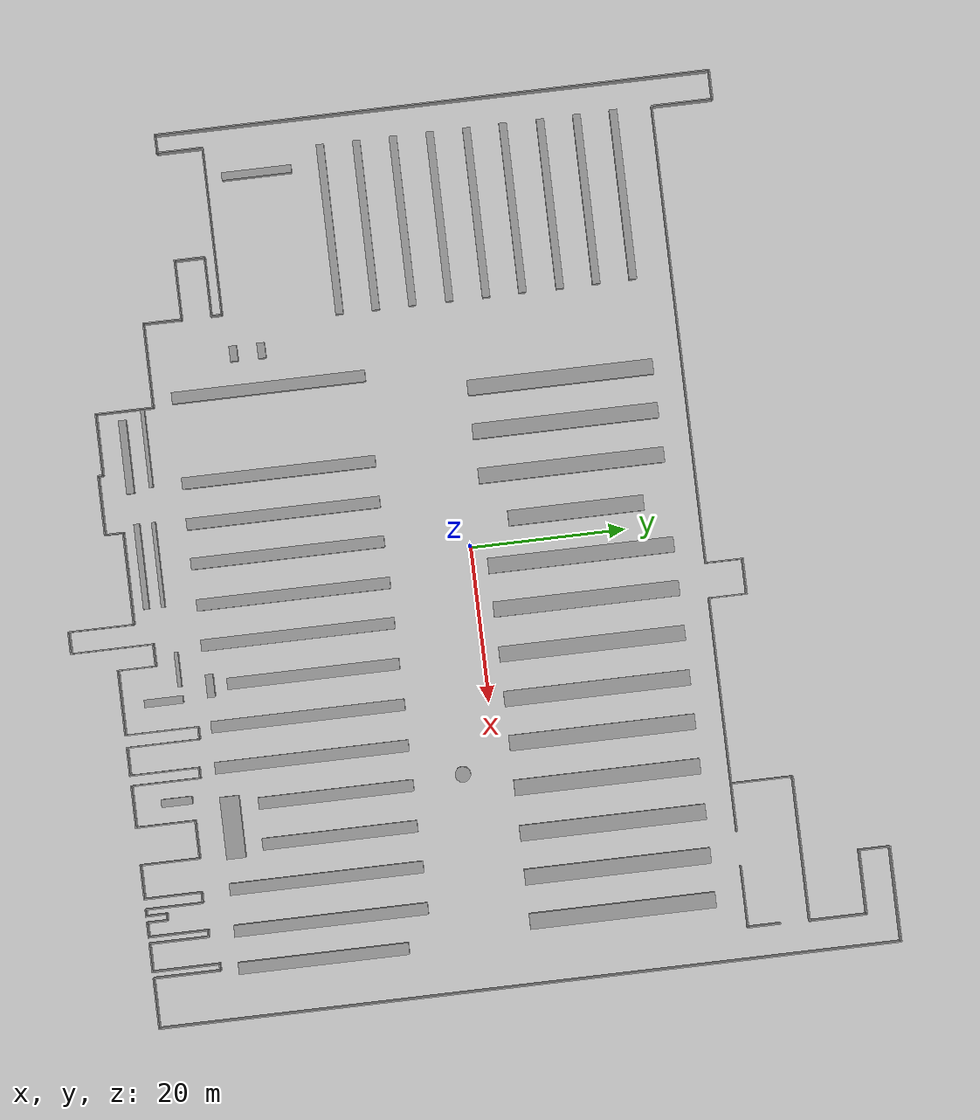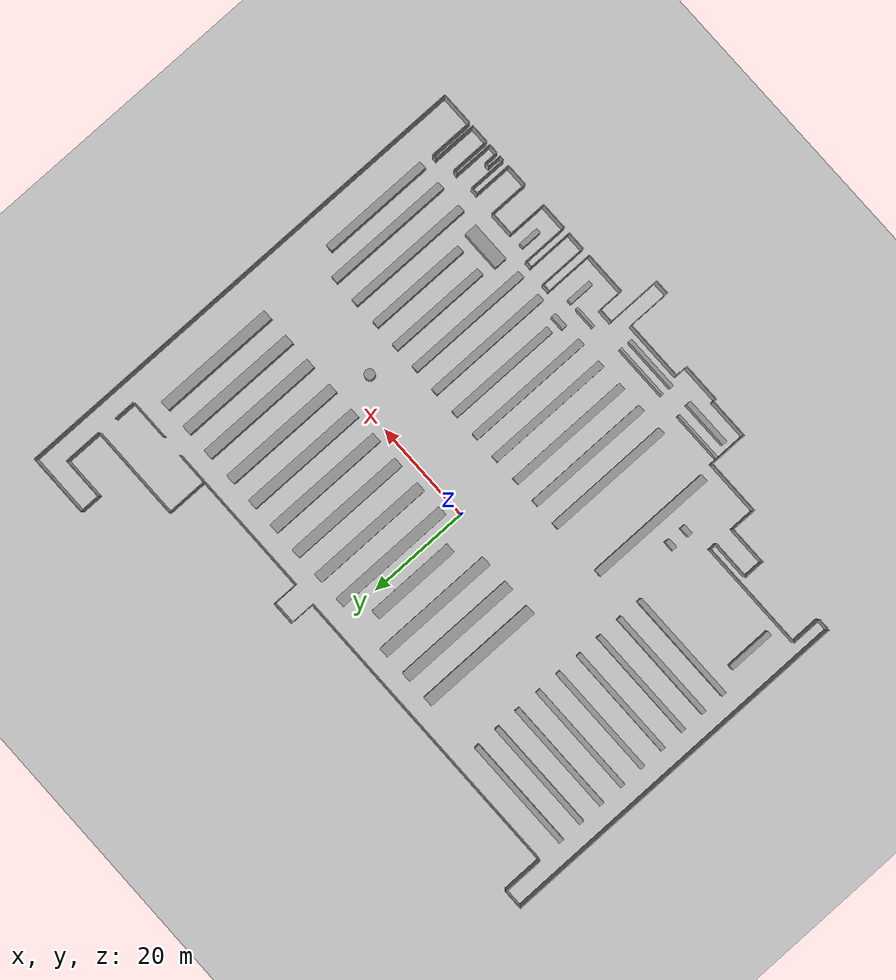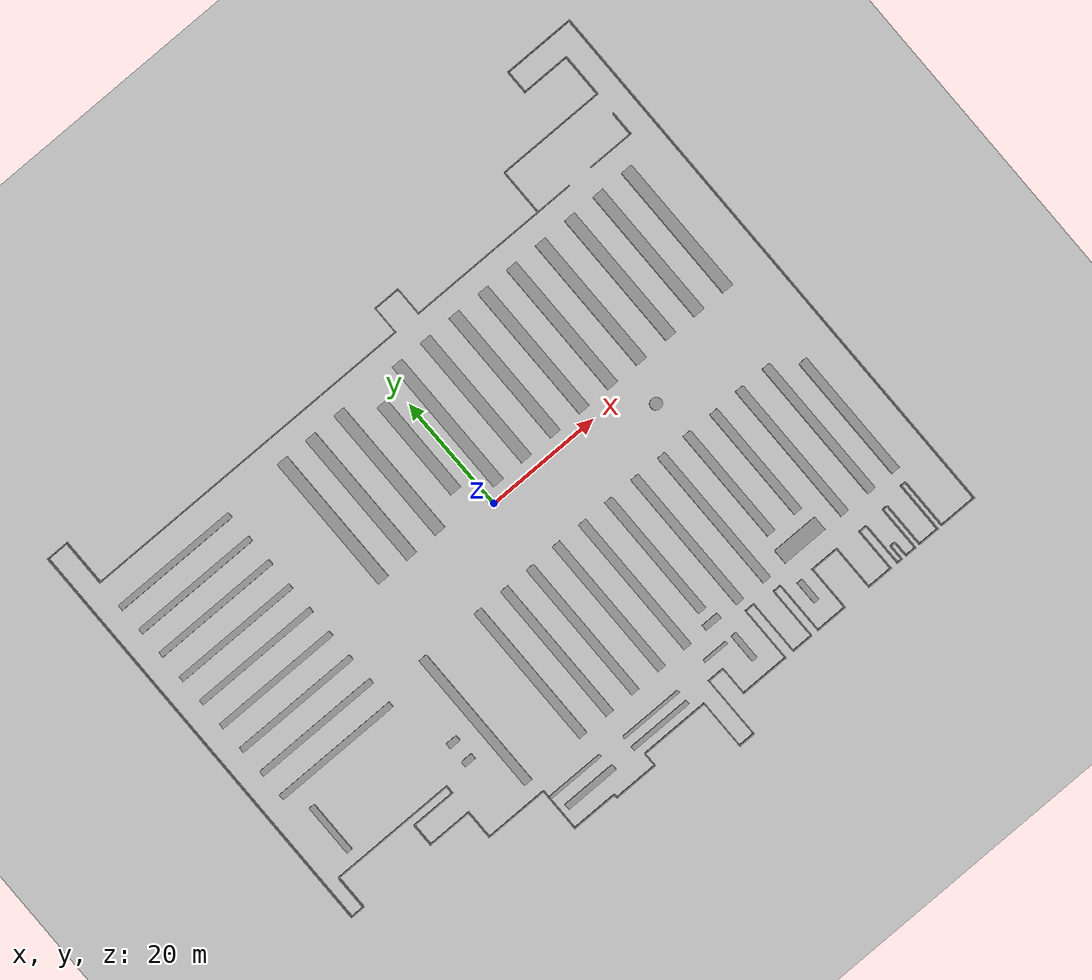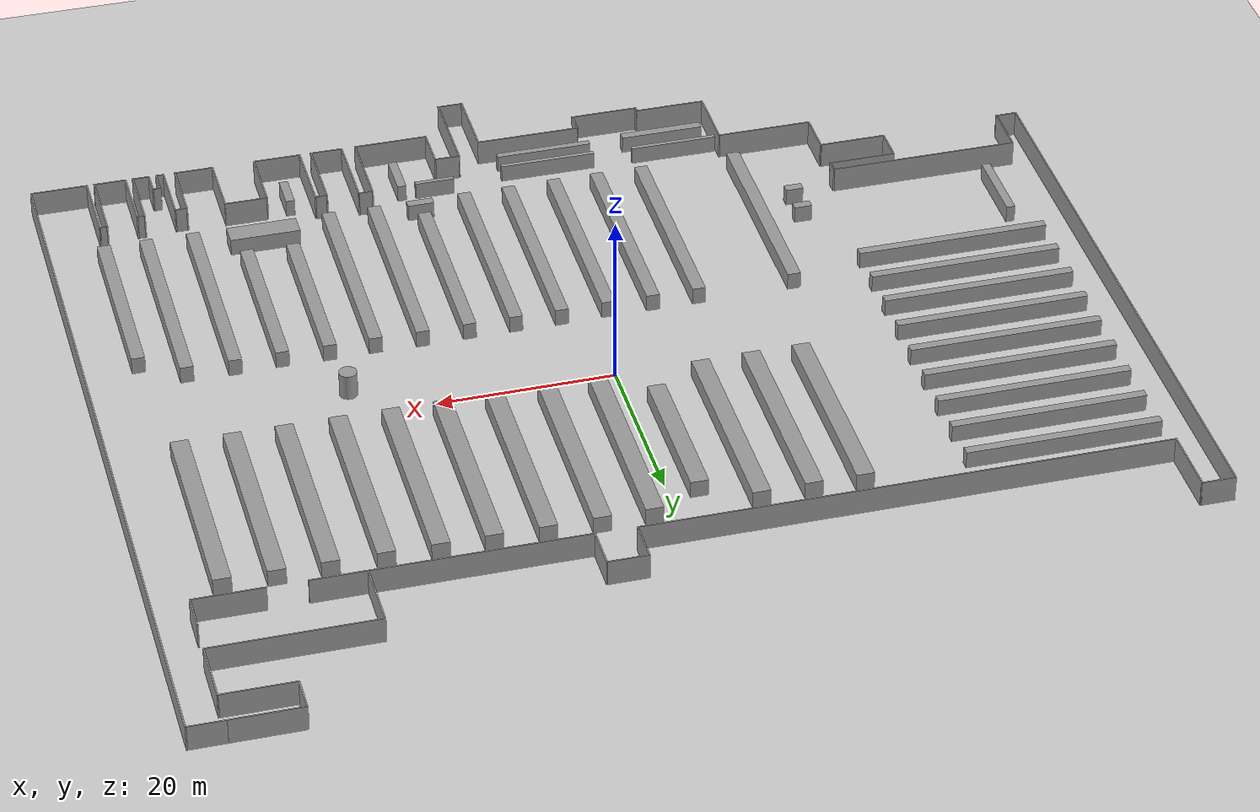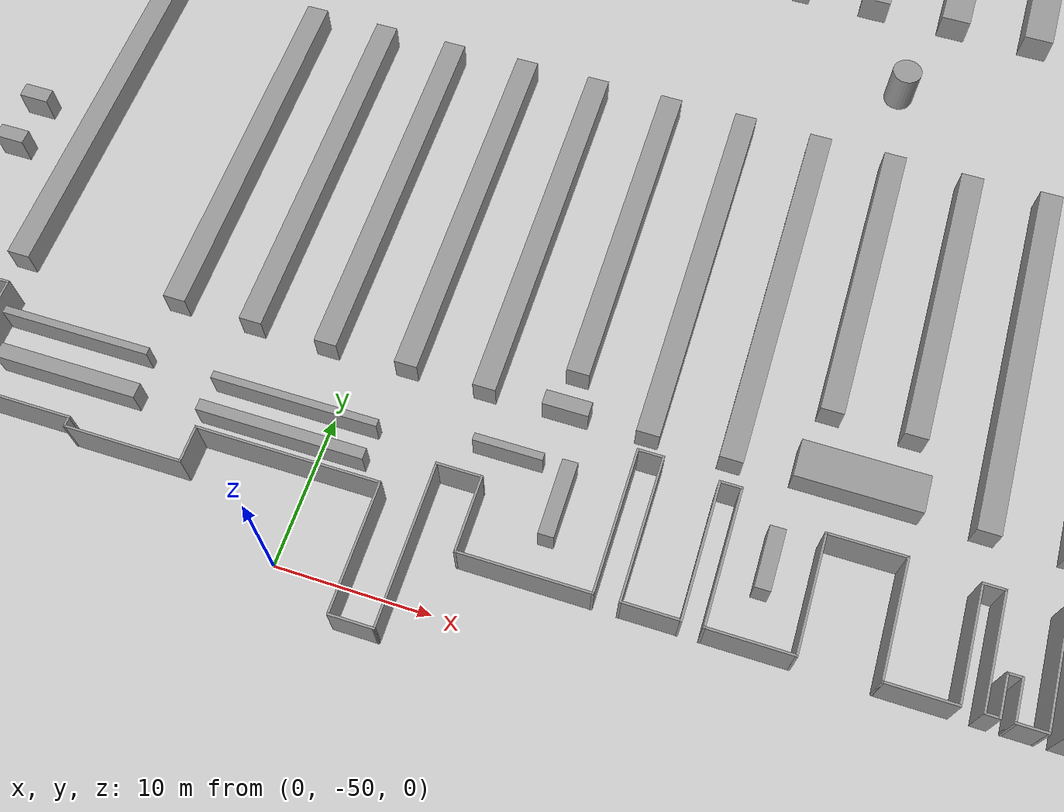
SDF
<sdf version="1.6">
 <world name="default">
  <light name="sun" type="directional">
   <pose>0 0 10 0 -0 0</pose>
   <diffuse>0.8 0.8 0.8 1</diffuse>
   <specular>0.2 0.2 0.2 1</specular>
   <attenuation>
    <range>1000</range>
    <constant>0.9</constant>
    <linear>0.01</linear>
    <quadratic>0.001</quadratic>
   </attenuation>
   <direction>-0.5 0.1 -0.9</direction>
  </light>
  <model name="ground_plane">
   <static>1</static>
   <link name="link">
    <collision name="collision">
     <geometry><plane><normal>0 0 1</normal><size>120 120</size></plane></geometry>
     <surface>
      <contact><collide_bitmask>65535</collide_bitmask></contact>
      <friction><ode><mu>100</mu><mu2>50</mu2></ode></friction>
     </surface>
    </collision>
    <visual name="visual">
     <cast_shadows>0</cast_shadows>
     <geometry><plane><normal>0 0 1</normal><size>120 120</size></plane></geometry>
     <material>
      <script><uri>file://media/materials/scripts/gazebo.material</uri><name>Gazebo/Grey</name></script>
     </material>
    </visual>
   </link>
  </model>
  <gravity>0 0 -9.8</gravity>
  <magnetic_field>6e-06 2.3e-05 -4.2e-05</magnetic_field>
  <atmosphere type="adiabatic"/>
  <physics name="default_physics" default="0" type="ode">
   <max_step_size>0.001</max_step_size>
   <real_time_factor>1</real_time_factor>
   <real_time_update_rate>1000</real_time_update_rate>
  </physics>
  <scene><ambient>0.4 0.4 0.4 1</ambient><background>0.7 0.7 0.7 1</background><shadows>1</shadows></scene>
  <spherical_coordinates>
   <surface_model>EARTH_WGS84</surface_model>
   <latitude_deg>0</latitude_deg>
   <longitude_deg>0</longitude_deg>
   <elevation>0</elevation>
   <heading_deg>0</heading_deg>
  </spherical_coordinates>
  <model name="walls">
   <pose>-0.3813 -1.8007 0 0 -0 0</pose>
   <link name="Wall_0">
    <collision name="Wall_0_Collision">
     <geometry><box><size>21.75 0.15 3</size></box></geometry>
     <pose>0 0 1.5 0 -0 0</pose>
    </collision>
    <visual name="Wall_0_Visual">
     <pose>0 0 1.5 0 -0 0</pose>
     <geometry><box><size>21.75 0.15 3</size></box></geometry>
     <material>
      <script><uri>file://media/materials/scripts/gazebo.material</uri><name>Gazebo/Grey</name></script>
      <ambient>1 1 1 1</ambient>
     </material>
     <meta><layer>0</layer></meta>
    </visual>
    <pose>-43.7799 -26.4633 0 0 -0 3.14159</pose>
   </link>
   <link name="Wall_1">
    <collision name="Wall_1_Collision">
     <geometry><box><size>6 0.15 3</size></box></geometry>
     <pose>0 0 1.5 0 -0 0</pose>
    </collision>
    <visual name="Wall_1_Visual">
     <pose>0 0 1.5 0 -0 0</pose>
     <geometry><box><size>6 0.15 3</size></box></geometry>
     <material>
      <script><uri>file://media/materials/scripts/gazebo.material</uri><name>Gazebo/Grey</name></script>
      <ambient>1 1 1 1</ambient>
     </material>
     <meta><layer>0</layer></meta>
    </visual>
    <pose>-54.5799 -29.3883 0 0 -0 -1.5708</pose>
   </link>
   <link name="Wall_10">
    <collision name="Wall_10_Collision">
     <geometry><box><size>4.25 0.15 3</size></box></geometry>
     <pose>0 0 1.5 0 -0 0</pose>
    </collision>
    <visual name="Wall_10_Visual">
     <pose>0 0 1.5 0 -0 0</pose>
     <geometry><box><size>4.25 0.15 3</size></box></geometry>
     <material>
      <script><uri>file://media/materials/scripts/gazebo.material</uri><name>Gazebo/Grey</name></script>
      <ambient>1 1 1 1</ambient>
     </material>
     <meta><layer>0</layer></meta>
    </visual>
    <pose>52.8619 33.4688 0 0 -0 1.5708</pose>
   </link>
   <link name="Wall_100">
    <collision name="Wall_100_Collision">
     <geometry><box><size>3.9 0.15 3</size></box></geometry>
     <pose>0 0 1.5 0 -0 0</pose>
    </collision>
    <visual name="Wall_100_Visual">
     <pose>0 0 1.5 0 -0 0</pose>
     <geometry><box><size>3.9 0.15 3</size></box></geometry>
     <material>
      <script><uri>file://media/materials/scripts/gazebo.material</uri><name>Gazebo/Grey</name></script>
      <ambient>1 1 1 1</ambient>
     </material>
     <meta><layer>0</layer></meta>
    </visual>
    <pose>-55.0561 39.3752 0 0 -0 3.14159</pose>
   </link>
   <link name="Wall_102">
    <collision name="Wall_102_Collision">
     <geometry><box><size>7.75 0.15 3</size></box></geometry>
     <pose>0 0 1.5 0 -0 0</pose>
    </collision>
    <visual name="Wall_102_Visual">
     <pose>0 0 1.5 0 -0 0</pose>
     <geometry><box><size>7.75 0.15 3</size></box></geometry>
     <material>
      <script><uri>file://media/materials/scripts/gazebo.material</uri><name>Gazebo/Grey</name></script>
      <ambient>1 1 1 1</ambient>
     </material>
     <meta><layer>0</layer></meta>
    </visual>
    <pose>-36.7799 -27.8133 0 0 -0 3.14159</pose>
   </link>
   <link name="Wall_103">
    <collision name="Wall_103_Collision">
     <geometry><box><size>4 0.15 3</size></box></geometry>
     <pose>0 0 1.5 0 -0 0</pose>
    </collision>
    <visual name="Wall_103_Visual">
     <pose>0 0 1.5 0 -0 0</pose>
     <geometry><box><size>4 0.15 3</size></box></geometry>
     <material>
      <script><uri>file://media/materials/scripts/gazebo.material</uri><name>Gazebo/Grey</name></script>
      <ambient>1 1 1 1</ambient>
     </material>
     <meta><layer>0</layer></meta>
    </visual>
    <pose>-40.5799 -29.7383 0 0 -0 -1.5708</pose>
   </link>
   <link name="Wall_104">
    <collision name="Wall_104_Collision">
     <geometry><box><size>7.75 0.15 3</size></box></geometry>
     <pose>0 0 1.5 0 -0 0</pose>
    </collision>
    <visual name="Wall_104_Visual">
     <pose>0 0 1.5 0 -0 0</pose>
     <geometry><box><size>7.75 0.15 3</size></box></geometry>
     <material>
      <script><uri>file://media/materials/scripts/gazebo.material</uri><name>Gazebo/Grey</name></script>
      <ambient>1 1 1 1</ambient>
     </material>
     <meta><layer>0</layer></meta>
    </visual>
    <pose>-36.7799 -31.6633 0 0 -0 0</pose>
   </link>
   <link name="Wall_110">
    <collision name="Wall_110_Collision">
     <geometry><box><size>11 0.15 3</size></box></geometry>
     <pose>0 0 1.5 0 -0 0</pose>
    </collision>
    <visual name="Wall_110_Visual">
     <pose>0 0 1.5 0 -0 0</pose>
     <geometry><box><size>11 0.15 3</size></box></geometry>
     <material>
      <script><uri>file://media/materials/scripts/gazebo.material</uri><name>Gazebo/Grey</name></script>
      <ambient>1 1 1 1</ambient>
     </material>
     <meta><layer>0</layer></meta>
    </visual>
    <pose>-27.5715 -36.575 0 0 -0 3.14159</pose>
   </link>
   <link name="Wall_111">
    <collision name="Wall_111_Collision">
     <geometry><box><size>5.06174 0.15 3</size></box></geometry>
     <pose>0 0 1.5 0 -0 0</pose>
    </collision>
    <visual name="Wall_111_Visual">
     <pose>0 0 1.5 0 -0 0</pose>
     <geometry><box><size>5.06174 0.15 3</size></box></geometry>
     <material>
      <script><uri>file://media/materials/scripts/gazebo.material</uri><name>Gazebo/Grey</name></script>
      <ambient>1 1 1 1</ambient>
     </material>
     <meta><layer>0</layer></meta>
    </visual>
    <pose>-32.9882 -34.1191 0 0 -0 1.56743</pose>
   </link>
   <link name="Wall_113">
    <collision name="Wall_113_Collision">
     <geometry><box><size>2.5 0.15 3</size></box></geometry>
     <pose>0 0 1.5 0 -0 0</pose>
    </collision>
    <visual name="Wall_113_Visual">
     <pose>0 0 1.5 0 -0 0</pose>
     <geometry><box><size>2.5 0.15 3</size></box></geometry>
     <material>
      <script><uri>file://media/materials/scripts/gazebo.material</uri><name>Gazebo/Grey</name></script>
      <ambient>1 1 1 1</ambient>
     </material>
     <meta><layer>0</layer></meta>
    </visual>
    <pose>-6.64678 -43.4103 0 0 -0 -1.5708</pose>
   </link>
   <link name="Wall_114">
    <collision name="Wall_114_Collision">
     <geometry><box><size>7.75 0.15 3</size></box></geometry>
     <pose>0 0 1.5 0 -0 0</pose>
    </collision>
    <visual name="Wall_114_Visual">
     <pose>0 0 1.5 0 -0 0</pose>
     <geometry><box><size>7.75 0.15 3</size></box></geometry>
     <material>
      <script><uri>file://media/materials/scripts/gazebo.material</uri><name>Gazebo/Grey</name></script>
      <ambient>1 1 1 1</ambient>
     </material>
     <meta><layer>0</layer></meta>
    </visual>
    <pose>-10.4468 -44.5853 0 0 -0 3.14159</pose>
   </link>
   <link name="Wall_116">
    <collision name="Wall_116_Collision">
     <geometry><box><size>0.75 0.15 3</size></box></geometry>
     <pose>0 0 1.5 0 -0 0</pose>
    </collision>
    <visual name="Wall_116_Visual">
     <pose>0 0 1.5 0 -0 0</pose>
     <geometry><box><size>0.75 0.15 3</size></box></geometry>
     <material>
      <script><uri>file://media/materials/scripts/gazebo.material</uri><name>Gazebo/Grey</name></script>
      <ambient>1 1 1 1</ambient>
     </material>
     <meta><layer>0</layer></meta>
    </visual>
    <pose>-14.2468 -44.2853 0 0 -0 1.5708</pose>
   </link>
   <link name="Wall_117">
    <collision name="Wall_117_Collision">
     <geometry><box><size>8.05 0.15 3</size></box></geometry>
     <pose>0 0 1.5 0 -0 0</pose>
    </collision>
    <visual name="Wall_117_Visual">
     <pose>0 0 1.5 0 -0 0</pose>
     <geometry><box><size>8.05 0.15 3</size></box></geometry>
     <material>
      <script><uri>file://media/materials/scripts/gazebo.material</uri><name>Gazebo/Grey</name></script>
      <ambient>1 1 1 1</ambient>
     </material>
     <meta><layer>0</layer></meta>
    </visual>
    <pose>-18.1968 -43.9853 0 0 -0 3.14159</pose>
   </link>
   <link name="Wall_119">
    <collision name="Wall_119_Collision">
     <geometry><box><size>8.5 0.15 3</size></box></geometry>
     <pose>0 0 1.5 0 -0 0</pose>
    </collision>
    <visual name="Wall_119_Visual">
     <pose>0 0 1.5 0 -0 0</pose>
     <geometry><box><size>8.5 0.15 3</size></box></geometry>
     <material>
      <script><uri>file://media/materials/scripts/gazebo.material</uri><name>Gazebo/Grey</name></script>
      <ambient>1 1 1 1</ambient>
     </material>
     <meta><layer>0</layer></meta>
    </visual>
    <pose>5.20322 -46.4103 0 0 -0 -1.5708</pose>
   </link>
   <link name="Wall_12">
    <collision name="Wall_12_Collision">
     <geometry><box><size>18.75 0.15 3</size></box></geometry>
     <pose>0 0 1.5 0 -0 0</pose>
    </collision>
    <visual name="Wall_12_Visual">
     <pose>0 0 1.5 0 -0 0</pose>
     <geometry><box><size>18.75 0.15 3</size></box></geometry>
     <material>
      <script><uri>file://media/materials/scripts/gazebo.material</uri><name>Gazebo/Grey</name></script>
      <ambient>1 1 1 1</ambient>
     </material>
     <meta><layer>0</layer></meta>
    </visual>
    <pose>43.6596 39.3448 0 0 -0 3.14159</pose>
   </link>
   <link name="Wall_123">
    <collision name="Wall_123_Collision">
     <geometry><box><size>10.7438 0.15 3</size></box></geometry>
     <pose>0 0 1.5 0 -0 0</pose>
    </collision>
    <visual name="Wall_123_Visual">
     <pose>0 0 1.5 0 -0 0</pose>
     <geometry><box><size>10.7438 0.15 3</size></box></geometry>
     <material>
      <script><uri>file://media/materials/scripts/gazebo.material</uri><name>Gazebo/Grey</name></script>
      <ambient>1 1 1 1</ambient>
     </material>
     <meta><layer>0</layer></meta>
    </visual>
    <pose>7.99251 -45.3591 0 0 -0 -1.57021</pose>
   </link>
   <link name="Wall_126">
    <collision name="Wall_126_Collision">
     <geometry><box><size>8.25 0.15 3</size></box></geometry>
     <pose>0 0 1.5 0 -0 0</pose>
    </collision>
    <visual name="Wall_126_Visual">
     <pose>0 0 1.5 0 -0 0</pose>
     <geometry><box><size>8.25 0.15 3</size></box></geometry>
     <material>
      <script><uri>file://media/materials/scripts/gazebo.material</uri><name>Gazebo/Grey</name></script>
      <ambient>1 1 1 1</ambient>
     </material>
     <meta><layer>0</layer></meta>
    </visual>
    <pose>48.7751 50.656 0 0 -0 3.14159</pose>
   </link>
   <link name="Wall_127">
    <collision name="Wall_127_Collision">
     <geometry><box><size>3.97 0.15 3</size></box></geometry>
     <pose>0 0 1.5 0 -0 0</pose>
    </collision>
    <visual name="Wall_127_Visual">
     <pose>0 0 1.5 0 -0 0</pose>
     <geometry><box><size>3.97 0.15 3</size></box></geometry>
     <material>
      <script><uri>file://media/materials/scripts/gazebo.material</uri><name>Gazebo/Grey</name></script>
      <ambient>1 1 1 1</ambient>
     </material>
     <meta><layer>0</layer></meta>
    </visual>
    <pose>44.7251 48.606 0 0 -0 -1.5708</pose>
   </link>
   <link name="Wall_130">
    <collision name="Wall_130_Collision">
     <geometry><box><size>2.93 0.15 3</size></box></geometry>
     <pose>0 0 1.5 0 -0 0</pose>
    </collision>
    <visual name="Wall_130_Visual">
     <pose>0 0 1.5 0 -0 0</pose>
     <geometry><box><size>2.93 0.15 3</size></box></geometry>
     <material>
      <script><uri>file://media/materials/scripts/gazebo.material</uri><name>Gazebo/Grey</name></script>
      <ambient>1 1 1 1</ambient>
     </material>
     <meta><layer>0</layer></meta>
    </visual>
    <pose>6.6056 -50.656 0 0 -0 3.14159</pose>
   </link>
   <link name="Wall_14">
    <collision name="Wall_14_Collision">
     <geometry><box><size>7.5 0.15 3</size></box></geometry>
     <pose>0 0 1.5 0 -0 0</pose>
    </collision>
    <visual name="Wall_14_Visual">
     <pose>0 0 1.5 0 -0 0</pose>
     <geometry><box><size>7.5 0.15 3</size></box></geometry>
     <material>
      <script><uri>file://media/materials/scripts/gazebo.material</uri><name>Gazebo/Grey</name></script>
      <ambient>1 1 1 1</ambient>
     </material>
     <meta><layer>0</layer></meta>
    </visual>
    <pose>52.9596 43.0198 0 0 -0 1.5708</pose>
   </link>
   <link name="Wall_15">
    <collision name="Wall_15_Collision">
     <geometry><box><size>8.25 0.15 3</size></box></geometry>
     <pose>0 0 1.5 0 -0 0</pose>
    </collision>
    <visual name="Wall_15_Visual">
     <pose>0 0 1.5 0 -0 0</pose>
     <geometry><box><size>8.25 0.15 3</size></box></geometry>
     <material>
      <script><uri>file://media/materials/scripts/gazebo.material</uri><name>Gazebo/Grey</name></script>
      <ambient>1 1 1 1</ambient>
     </material>
     <meta><layer>0</layer></meta>
    </visual>
    <pose>48.9096 46.6948 0 0 -0 3.14159</pose>
   </link>
   <link name="Wall_17">
    <collision name="Wall_17_Collision">
     <geometry><box><size>4.25 0.15 3</size></box></geometry>
     <pose>0 0 1.5 0 -0 0</pose>
    </collision>
    <visual name="Wall_17_Visual">
     <pose>0 0 1.5 0 -0 0</pose>
     <geometry><box><size>4.25 0.15 3</size></box></geometry>
     <material>
      <script><uri>file://media/materials/scripts/gazebo.material</uri><name>Gazebo/Grey</name></script>
      <ambient>1 1 1 1</ambient>
     </material>
     <meta><layer>0</layer></meta>
    </visual>
    <pose>54.8751 50.656 0 0 -0 0</pose>
   </link>
   <link name="Wall_2">
    <collision name="Wall_2_Collision">
     <geometry><box><size>2.5 0.15 3</size></box></geometry>
     <pose>0 0 1.5 0 -0 0</pose>
    </collision>
    <visual name="Wall_2_Visual">
     <pose>0 0 1.5 0 -0 0</pose>
     <geometry><box><size>2.5 0.15 3</size></box></geometry>
     <material>
      <script><uri>file://media/materials/scripts/gazebo.material</uri><name>Gazebo/Grey</name></script>
      <ambient>1 1 1 1</ambient>
     </material>
     <meta><layer>0</layer></meta>
    </visual>
    <pose>-55.7549 -32.3132 0 0 -0 3.14159</pose>
   </link>
   <link name="Wall_3">
    <collision name="Wall_3_Collision">
     <geometry><box><size>71.75 0.15 3</size></box></geometry>
     <pose>0 0 1.5 0 -0 0</pose>
    </collision>
    <visual name="Wall_3_Visual">
     <pose>0 0 1.5 0 -0 0</pose>
     <geometry><box><size>71.75 0.15 3</size></box></geometry>
     <material>
      <script><uri>file://media/materials/scripts/gazebo.material</uri><name>Gazebo/Grey</name></script>
      <ambient>1 1 1 1</ambient>
     </material>
     <meta><layer>0</layer></meta>
    </visual>
    <pose>-56.9299 3.48675 0 0 -0 1.5708</pose>
   </link>
   <link name="Wall_33">
    <collision name="Wall_33_Collision">
     <geometry><box><size>1.5 0.15 3</size></box></geometry>
     <pose>0 0 1.5 0 -0 0</pose>
    </collision>
    <visual name="Wall_33_Visual">
     <pose>0 0 1.5 0 -0 0</pose>
     <geometry><box><size>1.5 0.15 3</size></box></geometry>
     <material>
      <script><uri>file://media/materials/scripts/gazebo.material</uri><name>Gazebo/Grey</name></script>
      <ambient>1 1 1 1</ambient>
     </material>
     <meta><layer>0</layer></meta>
    </visual>
    <pose>-32.9799 -27.1383 0 0 -0 -1.5708</pose>
   </link>
   <link name="Wall_37">
    <collision name="Wall_37_Collision">
     <geometry><box><size>7.5 0.15 3</size></box></geometry>
     <pose>0 0 1.5 0 -0 0</pose>
    </collision>
    <visual name="Wall_37_Visual">
     <pose>0 0 1.5 0 -0 0</pose>
     <geometry><box><size>7.5 0.15 3</size></box></geometry>
     <material>
      <script><uri>file://media/materials/scripts/gazebo.material</uri><name>Gazebo/Grey</name></script>
      <ambient>1 1 1 1</ambient>
     </material>
     <meta><layer>0</layer></meta>
    </visual>
    <pose>-22.1465 -40.25 0 0 -0 -1.5708</pose>
   </link>
   <link name="Wall_41">
    <collision name="Wall_41_Collision">
     <geometry><box><size>12 0.15 3</size></box></geometry>
     <pose>0 0 1.5 0 -0 0</pose>
    </collision>
    <visual name="Wall_41_Visual">
     <pose>0 0 1.5 0 -0 0</pose>
     <geometry><box><size>12 0.15 3</size></box></geometry>
     <material>
      <script><uri>file://media/materials/scripts/gazebo.material</uri><name>Gazebo/Grey</name></script>
      <ambient>1 1 1 1</ambient>
     </material>
     <meta><layer>0</layer></meta>
    </visual>
    <pose>-0.721776 -42.2353 0 0 -0 0</pose>
   </link>
   <link name="Wall_44">
    <collision name="Wall_44_Collision">
     <geometry><box><size>3 0.15 3</size></box></geometry>
     <pose>0 0 1.5 0 -0 0</pose>
    </collision>
    <visual name="Wall_44_Visual">
     <pose>0 0 1.5 0 -0 0</pose>
     <geometry><box><size>3 0.15 3</size></box></geometry>
     <material>
      <script><uri>file://media/materials/scripts/gazebo.material</uri><name>Gazebo/Grey</name></script>
      <ambient>1 1 1 1</ambient>
     </material>
     <meta><layer>0</layer></meta>
    </visual>
    <pose>9.41442 -40.0622 0 0 -0 0</pose>
   </link>
   <link name="Wall_45">
    <collision name="Wall_45_Collision">
     <geometry><box><size>5.0287 0.15 3</size></box></geometry>
     <pose>0 0 1.5 0 -0 0</pose>
    </collision>
    <visual name="Wall_45_Visual">
     <pose>0 0 1.5 0 -0 0</pose>
     <geometry><box><size>5.0287 0.15 3</size></box></geometry>
     <material>
      <script><uri>file://media/materials/scripts/gazebo.material</uri><name>Gazebo/Grey</name></script>
      <ambient>1 1 1 1</ambient>
     </material>
     <meta><layer>0</layer></meta>
    </visual>
    <pose>10.8394 -42.5015 0 0 -0 -1.5708</pose>
   </link>
   <link name="Wall_46">
    <collision name="Wall_46_Collision">
     <geometry><box><size>8.5 0.15 3</size></box></geometry>
     <pose>0 0 1.5 0 -0 0</pose>
    </collision>
    <visual name="Wall_46_Visual">
     <pose>0 0 1.5 0 -0 0</pose>
     <geometry><box><size>8.5 0.15 3</size></box></geometry>
     <material>
      <script><uri>file://media/materials/scripts/gazebo.material</uri><name>Gazebo/Grey</name></script>
      <ambient>1 1 1 1</ambient>
     </material>
     <meta><layer>0</layer></meta>
    </visual>
    <pose>15.0144 -44.9305 0 0 -0 0</pose>
   </link>
   <link name="Wall_47">
    <collision name="Wall_47_Collision">
     <geometry><box><size>9.5287 0.15 3</size></box></geometry>
     <pose>0 0 1.5 0 -0 0</pose>
    </collision>
    <visual name="Wall_47_Visual">
     <pose>0 0 1.5 0 -0 0</pose>
     <geometry><box><size>9.5287 0.15 3</size></box></geometry>
     <material>
      <script><uri>file://media/materials/scripts/gazebo.material</uri><name>Gazebo/Grey</name></script>
      <ambient>1 1 1 1</ambient>
     </material>
     <meta><layer>0</layer></meta>
    </visual>
    <pose>19.1894 -40.2515 0 0 -0 1.5708</pose>
   </link>
   <link name="Wall_48">
    <collision name="Wall_48_Collision">
     <geometry><box><size>1.75 0.15 3</size></box></geometry>
     <pose>0 0 1.5 0 -0 0</pose>
    </collision>
    <visual name="Wall_48_Visual">
     <pose>0 0 1.5 0 -0 0</pose>
     <geometry><box><size>1.75 0.15 3</size></box></geometry>
     <material>
      <script><uri>file://media/materials/scripts/gazebo.material</uri><name>Gazebo/Grey</name></script>
      <ambient>1 1 1 1</ambient>
     </material>
     <meta><layer>0</layer></meta>
    </visual>
    <pose>19.9894 -35.5622 0 0 -0 0</pose>
   </link>
   <link name="Wall_49">
    <collision name="Wall_49_Collision">
     <geometry><box><size>9.51834 0.15 3</size></box></geometry>
     <pose>0 0 1.5 0 -0 0</pose>
    </collision>
    <visual name="Wall_49_Visual">
     <pose>0 0 1.5 0 -0 0</pose>
     <geometry><box><size>9.51834 0.15 3</size></box></geometry>
     <material>
      <script><uri>file://media/materials/scripts/gazebo.material</uri><name>Gazebo/Grey</name></script>
      <ambient>1 1 1 1</ambient>
     </material>
     <meta><layer>0</layer></meta>
    </visual>
    <pose>20.7946 -40.2463 0 0 -0 -1.56969</pose>
   </link>
   <link name="Wall_5">
    <collision name="Wall_5_Collision">
     <geometry><box><size>59.25 0.15 3</size></box></geometry>
     <pose>0 0 1.5 0 -0 0</pose>
    </collision>
    <visual name="Wall_5_Visual">
     <pose>0 0 1.5 0 -0 0</pose>
     <geometry><box><size>59.25 0.15 3</size></box></geometry>
     <material>
      <script><uri>file://media/materials/scripts/gazebo.material</uri><name>Gazebo/Grey</name></script>
      <ambient>1 1 1 1</ambient>
     </material>
     <meta><layer>0</layer></meta>
    </visual>
    <pose>-23.6461 31.5252 0 0 -0 0</pose>
   </link>
   <link name="Wall_50">
    <collision name="Wall_50_Collision">
     <geometry><box><size>3.75 0.15 3</size></box></geometry>
     <pose>0 0 1.5 0 -0 0</pose>
    </collision>
    <visual name="Wall_50_Visual">
     <pose>0 0 1.5 0 -0 0</pose>
     <geometry><box><size>3.75 0.15 3</size></box></geometry>
     <material>
      <script><uri>file://media/materials/scripts/gazebo.material</uri><name>Gazebo/Grey</name></script>
      <ambient>1 1 1 1</ambient>
     </material>
     <meta><layer>0</layer></meta>
    </visual>
    <pose>22.5998 -44.9201 0 0 -0 0</pose>
   </link>
   <link name="Wall_51">
    <collision name="Wall_51_Collision">
     <geometry><box><size>9.01834 0.15 3</size></box></geometry>
     <pose>0 0 1.5 0 -0 0</pose>
    </collision>
    <visual name="Wall_51_Visual">
     <pose>0 0 1.5 0 -0 0</pose>
     <geometry><box><size>9.01834 0.15 3</size></box></geometry>
     <material>
      <script><uri>file://media/materials/scripts/gazebo.material</uri><name>Gazebo/Grey</name></script>
      <ambient>1 1 1 1</ambient>
     </material>
     <meta><layer>0</layer></meta>
    </visual>
    <pose>24.3946 -40.4963 0 0 -0 1.57197</pose>
   </link>
   <link name="Wall_52">
    <collision name="Wall_52_Collision">
     <geometry><box><size>1.5 0.15 3</size></box></geometry>
     <pose>0 0 1.5 0 -0 0</pose>
    </collision>
    <visual name="Wall_52_Visual">
     <pose>0 0 1.5 0 -0 0</pose>
     <geometry><box><size>1.5 0.15 3</size></box></geometry>
     <material>
      <script><uri>file://media/materials/scripts/gazebo.material</uri><name>Gazebo/Grey</name></script>
      <ambient>1 1 1 1</ambient>
     </material>
     <meta><layer>0</layer></meta>
    </visual>
    <pose>25.0644 -36.0622 0 0 -0 0</pose>
   </link>
   <link name="Wall_53">
    <collision name="Wall_53_Collision">
     <geometry><box><size>9.01713 0.15 3</size></box></geometry>
     <pose>0 0 1.5 0 -0 0</pose>
    </collision>
    <visual name="Wall_53_Visual">
     <pose>0 0 1.5 0 -0 0</pose>
     <geometry><box><size>9.01713 0.15 3</size></box></geometry>
     <material>
      <script><uri>file://media/materials/scripts/gazebo.material</uri><name>Gazebo/Grey</name></script>
      <ambient>1 1 1 1</ambient>
     </material>
     <meta><layer>0</layer></meta>
    </visual>
    <pose>25.7394 -40.4957 0 0 -0 -1.5708</pose>
   </link>
   <link name="Wall_54">
    <collision name="Wall_54_Collision">
     <geometry><box><size>5.5 0.15 3</size></box></geometry>
     <pose>0 0 1.5 0 -0 0</pose>
    </collision>
    <visual name="Wall_54_Visual">
     <pose>0 0 1.5 0 -0 0</pose>
     <geometry><box><size>5.5 0.15 3</size></box></geometry>
     <material>
      <script><uri>file://media/materials/scripts/gazebo.material</uri><name>Gazebo/Grey</name></script>
      <ambient>1 1 1 1</ambient>
     </material>
     <meta><layer>0</layer></meta>
    </visual>
    <pose>28.4144 -44.9189 0 0 -0 0</pose>
   </link>
   <link name="Wall_55">
    <collision name="Wall_55_Collision">
     <geometry><box><size>7.76713 0.15 3</size></box></geometry>
     <pose>0 0 1.5 0 -0 0</pose>
    </collision>
    <visual name="Wall_55_Visual">
     <pose>0 0 1.5 0 -0 0</pose>
     <geometry><box><size>7.76713 0.15 3</size></box></geometry>
     <material>
      <script><uri>file://media/materials/scripts/gazebo.material</uri><name>Gazebo/Grey</name></script>
      <ambient>1 1 1 1</ambient>
     </material>
     <meta><layer>0</layer></meta>
    </visual>
    <pose>31.0894 -41.1207 0 0 -0 1.5708</pose>
   </link>
   <link name="Wall_56">
    <collision name="Wall_56_Collision">
     <geometry><box><size>5 0.15 3</size></box></geometry>
     <pose>0 0 1.5 0 -0 0</pose>
    </collision>
    <visual name="Wall_56_Visual">
     <pose>0 0 1.5 0 -0 0</pose>
     <geometry><box><size>5 0.15 3</size></box></geometry>
     <material>
      <script><uri>file://media/materials/scripts/gazebo.material</uri><name>Gazebo/Grey</name></script>
      <ambient>1 1 1 1</ambient>
     </material>
     <meta><layer>0</layer></meta>
    </visual>
    <pose>33.5144 -37.3122 0 0 -0 0</pose>
   </link>
   <link name="Wall_57">
    <collision name="Wall_57_Collision">
     <geometry><box><size>7.75 0.15 3</size></box></geometry>
     <pose>0 0 1.5 0 -0 0</pose>
    </collision>
    <visual name="Wall_57_Visual">
     <pose>0 0 1.5 0 -0 0</pose>
     <geometry><box><size>7.75 0.15 3</size></box></geometry>
     <material>
      <script><uri>file://media/materials/scripts/gazebo.material</uri><name>Gazebo/Grey</name></script>
      <ambient>1 1 1 1</ambient>
     </material>
     <meta><layer>0</layer></meta>
    </visual>
    <pose>35.9394 -41.1122 0 0 -0 -1.5708</pose>
   </link>
   <link name="Wall_58">
    <collision name="Wall_58_Collision">
     <geometry><box><size>4.5 0.15 3</size></box></geometry>
     <pose>0 0 1.5 0 -0 0</pose>
    </collision>
    <visual name="Wall_58_Visual">
     <pose>0 0 1.5 0 -0 0</pose>
     <geometry><box><size>4.5 0.15 3</size></box></geometry>
     <material>
      <script><uri>file://media/materials/scripts/gazebo.material</uri><name>Gazebo/Grey</name></script>
      <ambient>1 1 1 1</ambient>
     </material>
     <meta><layer>0</layer></meta>
    </visual>
    <pose>38.1144 -44.9122 0 0 -0 0</pose>
   </link>
   <link name="Wall_59">
    <collision name="Wall_59_Collision">
     <geometry><box><size>7.5 0.15 3</size></box></geometry>
     <pose>0 0 1.5 0 -0 0</pose>
    </collision>
    <visual name="Wall_59_Visual">
     <pose>0 0 1.5 0 -0 0</pose>
     <geometry><box><size>7.5 0.15 3</size></box></geometry>
     <material>
      <script><uri>file://media/materials/scripts/gazebo.material</uri><name>Gazebo/Grey</name></script>
      <ambient>1 1 1 1</ambient>
     </material>
     <meta><layer>0</layer></meta>
    </visual>
    <pose>40.2894 -41.2372 0 0 -0 1.5708</pose>
   </link>
   <link name="Wall_60">
    <collision name="Wall_60_Collision">
     <geometry><box><size>1.5 0.15 3</size></box></geometry>
     <pose>0 0 1.5 0 -0 0</pose>
    </collision>
    <visual name="Wall_60_Visual">
     <pose>0 0 1.5 0 -0 0</pose>
     <geometry><box><size>1.5 0.15 3</size></box></geometry>
     <material>
      <script><uri>file://media/materials/scripts/gazebo.material</uri><name>Gazebo/Grey</name></script>
      <ambient>1 1 1 1</ambient>
     </material>
     <meta><layer>0</layer></meta>
    </visual>
    <pose>40.9644 -37.5622 0 0 -0 0</pose>
   </link>
   <link name="Wall_61">
    <collision name="Wall_61_Collision">
     <geometry><box><size>7.4988 0.15 3</size></box></geometry>
     <pose>0 0 1.5 0 -0 0</pose>
    </collision>
    <visual name="Wall_61_Visual">
     <pose>0 0 1.5 0 -0 0</pose>
     <geometry><box><size>7.4988 0.15 3</size></box></geometry>
     <material>
      <script><uri>file://media/materials/scripts/gazebo.material</uri><name>Gazebo/Grey</name></script>
      <ambient>1 1 1 1</ambient>
     </material>
     <meta><layer>0</layer></meta>
    </visual>
    <pose>41.6394 -41.2366 0 0 -0 -1.5708</pose>
   </link>
   <link name="Wall_68">
    <collision name="Wall_68_Collision">
     <geometry><box><size>1 0.15 3</size></box></geometry>
     <pose>0 0 1.5 0 -0 0</pose>
    </collision>
    <visual name="Wall_68_Visual">
     <pose>0 0 1.5 0 -0 0</pose>
     <geometry><box><size>1 0.15 3</size></box></geometry>
     <material>
      <script><uri>file://media/materials/scripts/gazebo.material</uri><name>Gazebo/Grey</name></script>
      <ambient>1 1 1 1</ambient>
     </material>
     <meta><layer>0</layer></meta>
    </visual>
    <pose>42.0644 -44.9213 0 0 -0 0</pose>
   </link>
   <link name="Wall_69">
    <collision name="Wall_69_Collision">
     <geometry><box><size>2.7488 0.15 3</size></box></geometry>
     <pose>0 0 1.5 0 -0 0</pose>
    </collision>
    <visual name="Wall_69_Visual">
     <pose>0 0 1.5 0 -0 0</pose>
     <geometry><box><size>2.7488 0.15 3</size></box></geometry>
     <material>
      <script><uri>file://media/materials/scripts/gazebo.material</uri><name>Gazebo/Grey</name></script>
      <ambient>1 1 1 1</ambient>
     </material>
     <meta><layer>0</layer></meta>
    </visual>
    <pose>42.4894 -43.6116 0 0 -0 1.5708</pose>
   </link>
   <link name="Wall_7">
    <collision name="Wall_7_Collision">
     <geometry><box><size>30.25 0.15 3</size></box></geometry>
     <pose>0 0 1.5 0 -0 0</pose>
    </collision>
    <visual name="Wall_7_Visual">
     <pose>0 0 1.5 0 -0 0</pose>
     <geometry><box><size>30.25 0.15 3</size></box></geometry>
     <material>
      <script><uri>file://media/materials/scripts/gazebo.material</uri><name>Gazebo/Grey</name></script>
      <ambient>1 1 1 1</ambient>
     </material>
     <meta><layer>0</layer></meta>
    </visual>
    <pose>25.4816 31.4188 0 0 -0 0</pose>
   </link>
   <link name="Wall_70">
    <collision name="Wall_70_Collision">
     <geometry><box><size>1 0.15 3</size></box></geometry>
     <pose>0 0 1.5 0 -0 0</pose>
    </collision>
    <visual name="Wall_70_Visual">
     <pose>0 0 1.5 0 -0 0</pose>
     <geometry><box><size>1 0.15 3</size></box></geometry>
     <material>
      <script><uri>file://media/materials/scripts/gazebo.material</uri><name>Gazebo/Grey</name></script>
      <ambient>1 1 1 1</ambient>
     </material>
     <meta><layer>0</layer></meta>
    </visual>
    <pose>42.9144 -42.3122 0 0 -0 0</pose>
   </link>
   <link name="Wall_71">
    <collision name="Wall_71_Collision">
     <geometry><box><size>2.7799 0.15 3</size></box></geometry>
     <pose>0 0 1.5 0 -0 0</pose>
    </collision>
    <visual name="Wall_71_Visual">
     <pose>0 0 1.5 0 -0 0</pose>
     <geometry><box><size>2.7799 0.15 3</size></box></geometry>
     <material>
      <script><uri>file://media/materials/scripts/gazebo.material</uri><name>Gazebo/Grey</name></script>
      <ambient>1 1 1 1</ambient>
     </material>
     <meta><layer>0</layer></meta>
    </visual>
    <pose>43.3394 -43.6271 0 0 -0 -1.5708</pose>
   </link>
   <link name="Wall_72">
    <collision name="Wall_72_Collision">
     <geometry><box><size>2 0.15 3</size></box></geometry>
     <pose>0 0 1.5 0 -0 0</pose>
    </collision>
    <visual name="Wall_72_Visual">
     <pose>0 0 1.5 0 -0 0</pose>
     <geometry><box><size>2 0.15 3</size></box></geometry>
     <material>
      <script><uri>file://media/materials/scripts/gazebo.material</uri><name>Gazebo/Grey</name></script>
      <ambient>1 1 1 1</ambient>
     </material>
     <meta><layer>0</layer></meta>
    </visual>
    <pose>44.2644 -44.9317 0 0 -0 0</pose>
   </link>
   <link name="Wall_73">
    <collision name="Wall_73_Collision">
     <geometry><box><size>7.7799 0.15 3</size></box></geometry>
     <pose>0 0 1.5 0 -0 0</pose>
    </collision>
    <visual name="Wall_73_Visual">
     <pose>0 0 1.5 0 -0 0</pose>
     <geometry><box><size>7.7799 0.15 3</size></box></geometry>
     <material>
      <script><uri>file://media/materials/scripts/gazebo.material</uri><name>Gazebo/Grey</name></script>
      <ambient>1 1 1 1</ambient>
     </material>
     <meta><layer>0</layer></meta>
    </visual>
    <pose>45.1894 -41.1271 0 0 -0 1.5708</pose>
   </link>
   <link name="Wall_74">
    <collision name="Wall_74_Collision">
     <geometry><box><size>1 0.15 3</size></box></geometry>
     <pose>0 0 1.5 0 -0 0</pose>
    </collision>
    <visual name="Wall_74_Visual">
     <pose>0 0 1.5 0 -0 0</pose>
     <geometry><box><size>1 0.15 3</size></box></geometry>
     <material>
      <script><uri>file://media/materials/scripts/gazebo.material</uri><name>Gazebo/Grey</name></script>
      <ambient>1 1 1 1</ambient>
     </material>
     <meta><layer>0</layer></meta>
    </visual>
    <pose>45.6144 -37.3122 0 0 -0 0</pose>
   </link>
   <link name="Wall_75">
    <collision name="Wall_75_Collision">
     <geometry><box><size>7.76956 0.15 3</size></box></geometry>
     <pose>0 0 1.5 0 -0 0</pose>
    </collision>
    <visual name="Wall_75_Visual">
     <pose>0 0 1.5 0 -0 0</pose>
     <geometry><box><size>7.76956 0.15 3</size></box></geometry>
     <material>
      <script><uri>file://media/materials/scripts/gazebo.material</uri><name>Gazebo/Grey</name></script>
      <ambient>1 1 1 1</ambient>
     </material>
     <meta><layer>0</layer></meta>
    </visual>
    <pose>46.0394 -41.1219 0 0 -0 -1.5708</pose>
   </link>
   <link name="Wall_76">
    <collision name="Wall_76_Collision">
     <geometry><box><size>3.75 0.15 3</size></box></geometry>
     <pose>0 0 1.5 0 -0 0</pose>
    </collision>
    <visual name="Wall_76_Visual">
     <pose>0 0 1.5 0 -0 0</pose>
     <geometry><box><size>3.75 0.15 3</size></box></geometry>
     <material>
      <script><uri>file://media/materials/scripts/gazebo.material</uri><name>Gazebo/Grey</name></script>
      <ambient>1 1 1 1</ambient>
     </material>
     <meta><layer>0</layer></meta>
    </visual>
    <pose>47.8498 -44.9317 0 0 -0 0</pose>
   </link>
   <link name="Wall_77">
    <collision name="Wall_77_Collision">
     <geometry><box><size>8.76956 0.15 3</size></box></geometry>
     <pose>0 0 1.5 0 -0 0</pose>
    </collision>
    <visual name="Wall_77_Visual">
     <pose>0 0 1.5 0 -0 0</pose>
     <geometry><box><size>8.76956 0.15 3</size></box></geometry>
     <material>
      <script><uri>file://media/materials/scripts/gazebo.material</uri><name>Gazebo/Grey</name></script>
      <ambient>1 1 1 1</ambient>
     </material>
     <meta><layer>0</layer></meta>
    </visual>
    <pose>49.6394 -40.6219 0 0 -0 1.5708</pose>
   </link>
   <link name="Wall_78">
    <collision name="Wall_78_Collision">
     <geometry><box><size>1 0.15 3</size></box></geometry>
     <pose>0 0 1.5 0 -0 0</pose>
    </collision>
    <visual name="Wall_78_Visual">
     <pose>0 0 1.5 0 -0 0</pose>
     <geometry><box><size>1 0.15 3</size></box></geometry>
     <material>
      <script><uri>file://media/materials/scripts/gazebo.material</uri><name>Gazebo/Grey</name></script>
      <ambient>1 1 1 1</ambient>
     </material>
     <meta><layer>0</layer></meta>
    </visual>
    <pose>50.0644 -36.3122 0 0 -0 0</pose>
   </link>
   <link name="Wall_79">
    <collision name="Wall_79_Collision">
     <geometry><box><size>8.75 0.15 3</size></box></geometry>
     <pose>0 0 1.5 0 -0 0</pose>
    </collision>
    <visual name="Wall_79_Visual">
     <pose>0 0 1.5 0 -0 0</pose>
     <geometry><box><size>8.75 0.15 3</size></box></geometry>
     <material>
      <script><uri>file://media/materials/scripts/gazebo.material</uri><name>Gazebo/Grey</name></script>
      <ambient>1 1 1 1</ambient>
     </material>
     <meta><layer>0</layer></meta>
    </visual>
    <pose>50.4894 -40.6122 0 0 -0 -1.5708</pose>
   </link>
   <link name="Wall_84">
    <collision name="Wall_84_Collision">
     <geometry><box><size>95.7269 0.15 3</size></box></geometry>
     <pose>0 0 1.5 0 -0 0</pose>
    </collision>
    <visual name="Wall_84_Visual">
     <pose>0 0 1.5 0 -0 0</pose>
     <geometry><box><size>95.7269 0.15 3</size></box></geometry>
     <material>
      <script><uri>file://media/materials/scripts/gazebo.material</uri><name>Gazebo/Grey</name></script>
      <ambient>1 1 1 1</ambient>
     </material>
     <meta><layer>0</layer></meta>
    </visual>
    <pose>56.9275 2.86758 0 0 -0 -1.57075</pose>
   </link>
   <link name="Wall_86">
    <collision name="Wall_86_Collision">
     <geometry><box><size>6.55 0.15 3</size></box></geometry>
     <pose>0 0 1.5 0 -0 0</pose>
    </collision>
    <visual name="Wall_86_Visual">
     <pose>0 0 1.5 0 -0 0</pose>
     <geometry><box><size>6.55 0.15 3</size></box></geometry>
     <material>
      <script><uri>file://media/materials/scripts/gazebo.material</uri><name>Gazebo/Grey</name></script>
      <ambient>1 1 1 1</ambient>
     </material>
     <meta><layer>0</layer></meta>
    </visual>
    <pose>53.7092 -44.9209 0 0 -0 3.14159</pose>
   </link>
   <link name="Wall_88">
    <collision name="Wall_88_Collision">
     <geometry><box><size>8 0.15 3</size></box></geometry>
     <pose>0 0 1.5 0 -0 0</pose>
    </collision>
    <visual name="Wall_88_Visual">
     <pose>0 0 1.5 0 -0 0</pose>
     <geometry><box><size>8 0.15 3</size></box></geometry>
     <material>
      <script><uri>file://media/materials/scripts/gazebo.material</uri><name>Gazebo/Grey</name></script>
      <ambient>1 1 1 1</ambient>
     </material>
     <meta><layer>0</layer></meta>
    </visual>
    <pose>34.3596 35.4198 0 0 -0 -1.5708</pose>
   </link>
   <link name="Wall_9">
    <collision name="Wall_9_Collision">
     <geometry><box><size>8 0.15 3</size></box></geometry>
     <pose>0 0 1.5 0 -0 0</pose>
    </collision>
    <visual name="Wall_9_Visual">
     <pose>0 0 1.5 0 -0 0</pose>
     <geometry><box><size>8 0.15 3</size></box></geometry>
     <material>
      <script><uri>file://media/materials/scripts/gazebo.material</uri><name>Gazebo/Grey</name></script>
      <ambient>1 1 1 1</ambient>
     </material>
     <meta><layer>0</layer></meta>
    </visual>
    <pose>48.9369 31.4188 0 0 -0 0</pose>
   </link>
   <link name="Wall_90">
    <collision name="Wall_90_Collision">
     <geometry><box><size>4.75 0.15 3</size></box></geometry>
     <pose>0 0 1.5 0 -0 0</pose>
    </collision>
    <visual name="Wall_90_Visual">
     <pose>0 0 1.5 0 -0 0</pose>
     <geometry><box><size>4.75 0.15 3</size></box></geometry>
     <material>
      <script><uri>file://media/materials/scripts/gazebo.material</uri><name>Gazebo/Grey</name></script>
      <ambient>1 1 1 1</ambient>
     </material>
     <meta><layer>0</layer></meta>
    </visual>
    <pose>5.90393 33.8252 0 0 -0 1.5708</pose>
   </link>
   <link name="Wall_96">
    <collision name="Wall_96_Collision">
     <geometry><box><size>5 0.15 3</size></box></geometry>
     <pose>0 0 1.5 0 -0 0</pose>
    </collision>
    <visual name="Wall_96_Visual">
     <pose>0 0 1.5 0 -0 0</pose>
     <geometry><box><size>5 0.15 3</size></box></geometry>
     <material>
      <script><uri>file://media/materials/scripts/gazebo.material</uri><name>Gazebo/Grey</name></script>
      <ambient>1 1 1 1</ambient>
     </material>
     <meta><layer>0</layer></meta>
    </visual>
    <pose>10.4316 33.8438 0 0 -0 1.5708</pose>
   </link>
   <link name="Wall_97">
    <collision name="Wall_97_Collision">
     <geometry><box><size>4.6 0.15 3</size></box></geometry>
     <pose>0 0 1.5 0 -0 0</pose>
    </collision>
    <visual name="Wall_97_Visual">
     <pose>0 0 1.5 0 -0 0</pose>
     <geometry><box><size>4.6 0.15 3</size></box></geometry>
     <material>
      <script><uri>file://media/materials/scripts/gazebo.material</uri><name>Gazebo/Grey</name></script>
      <ambient>1 1 1 1</ambient>
     </material>
     <meta><layer>0</layer></meta>
    </visual>
    <pose>8.1316 36.2688 0 0 -0 3.14159</pose>
   </link>
   <link name="Wall_99">
    <collision name="Wall_99_Collision">
     <geometry><box><size>8 0.15 3</size></box></geometry>
     <pose>0 0 1.5 0 -0 0</pose>
    </collision>
    <visual name="Wall_99_Visual">
     <pose>0 0 1.5 0 -0 0</pose>
     <geometry><box><size>8 0.15 3</size></box></geometry>
     <material>
      <script><uri>file://media/materials/scripts/gazebo.material</uri><name>Gazebo/Grey</name></script>
      <ambient>1 1 1 1</ambient>
     </material>
     <meta><layer>0</layer></meta>
    </visual>
    <pose>-53.1961 35.4502 0 0 -0 1.5708</pose>
   </link>
   <static>1</static>
  </model>
  <model name="box3">
   <link name="link">
    <inertial>
     <mass>50</mass>
     <inertia><ixx>8.33333</ixx><ixy>0</ixy><ixz>0</ixz><iyy>8.33333</iyy><iyz>0</iyz><izz>8.33333</izz></inertia>
    </inertial>
    <pose>1.77498 -5.65946 0.5 0 -0 0</pose>
    <gravity>0</gravity>
    <visual name="visual">
     <geometry><box><size>10 0.5 2</size></box></geometry>
     <material>
      <script><name>Gazebo/Grey</name><uri>file://media/materials/scripts/gazebo.material</uri></script>
      <shader type="pixel"><normal_map>__default__</normal_map></shader>
      <ambient>0.3 0.3 0.3 1</ambient>
      <diffuse>0.7 0.7 0.7 1</diffuse>
      <specular>0.01 0.01 0.01 1</specular>
      <emissive>0 0 0 1</emissive>
     </material>
    </visual>
    <collision name="collision">
     <geometry><box><size>10 0.5 2</size></box></geometry>
     <surface>
      <friction>
       <ode><mu>1</mu><mu2>1</mu2><fdir1>0 0 0</fdir1><slip1>0</slip1><slip2>0</slip2></ode>
       <torsional>
        <coefficient>1</coefficient>
        <patch_radius>0</patch_radius>
        <surface_radius>0</surface_radius>
        <use_patch_radius>1</use_patch_radius>
        <ode><slip>0</slip></ode>
       </torsional>
      </friction>
      <bounce><restitution_coefficient>0</restitution_coefficient><threshold>1e+06</threshold></bounce>
      <contact>
       <collide_without_contact>0</collide_without_contact>
       <collide_without_contact_bitmask>1</collide_without_contact_bitmask>
       <collide_bitmask>1</collide_bitmask>
       <ode>
        <soft_cfm>0</soft_cfm>
        <soft_erp>0.2</soft_erp>
        <kp>1e+13</kp>
        <kd>1</kd>
        <max_vel>0.01</max_vel>
        <min_depth>0</min_depth>
       </ode>
       <bullet>
        <split_impulse>1</split_impulse>
        <split_impulse_penetration_threshold>-0.01</split_impulse_penetration_threshold>
        <soft_cfm>0</soft_cfm>
        <soft_erp>0.2</soft_erp>
        <kp>1e+13</kp>
        <kd>1</kd>
       </bullet>
      </contact>
     </surface>
    </collision>
   </link>
   <static>0</static>
   <pose>-19.1805 -34.1738 0.5 0 -0 0</pose>
  </model>
  <model name="box1">
   <link name="link">
    <inertial>
     <mass>50</mass>
     <inertia><ixx>354.167</ixx><ixy>0</ixy><ixz>0</ixz><iyy>20.8333</iyy><iyz>0</iyz><izz>341.667</izz></inertia>
    </inertial>
    <pose>-6.07242 -0.338776 0.500003 0 -0 0</pose>
    <visual name="visual">
     <geometry><box><size>1 9 2</size></box></geometry>
     <material>
      <script><name>Gazebo/Grey</name><uri>file://media/materials/scripts/gazebo.material</uri></script>
      <shader type="pixel"><normal_map>__default__</normal_map></shader>
      <ambient>0.3 0.3 0.3 1</ambient>
      <diffuse>0.7 0.7 0.7 1</diffuse>
      <specular>0.01 0.01 0.01 1</specular>
      <emissive>0 0 0 1</emissive>
     </material>
    </visual>
    <collision name="collision">
     <geometry><box><size>1 9 2</size></box></geometry>
     <surface>
      <friction>
       <ode><mu>1</mu><mu2>1</mu2><fdir1>0 0 0</fdir1><slip1>0</slip1><slip2>0</slip2></ode>
       <torsional>
        <coefficient>1</coefficient>
        <patch_radius>0</patch_radius>
        <surface_radius>0</surface_radius>
        <use_patch_radius>1</use_patch_radius>
        <ode><slip>0</slip></ode>
       </torsional>
      </friction>
      <bounce><restitution_coefficient>0</restitution_coefficient><threshold>1e+06</threshold></bounce>
      <contact>
       <collide_without_contact>0</collide_without_contact>
       <collide_without_contact_bitmask>1</collide_without_contact_bitmask>
       <collide_bitmask>1</collide_bitmask>
       <ode>
        <soft_cfm>0</soft_cfm>
        <soft_erp>0.2</soft_erp>
        <kp>1e+13</kp>
        <kd>1</kd>
        <max_vel>0.01</max_vel>
        <min_depth>0</min_depth>
       </ode>
       <bullet>
        <split_impulse>1</split_impulse>
        <split_impulse_penetration_threshold>-0.01</split_impulse_penetration_threshold>
        <soft_cfm>0</soft_cfm>
        <soft_erp>0.2</soft_erp>
        <kp>1e+13</kp>
        <kd>1</kd>
       </bullet>
      </contact>
     </surface>
    </collision>
   </link>
   <static>0</static>
   <pose>-44.9927 -21.3942 0.50001 0 -2e-06 0</pose>
  </model>
  <model name="box2">
   <link name="link">
    <inertial>
     <mass>50</mass>
     <inertia><ixx>8.33333</ixx><ixy>0</ixy><ixz>0</ixz><iyy>8.33333</iyy><iyz>0</iyz><izz>8.33333</izz></inertia>
    </inertial>
    <pose>5.5216 -2.84495 0.5 0 -0 0</pose>
    <gravity>0</gravity>
    <visual name="visual">
     <geometry><box><size>2 1 2</size></box></geometry>
     <material>
      <script><name>Gazebo/Grey</name><uri>file://media/materials/scripts/gazebo.material</uri></script>
      <shader type="pixel"><normal_map>__default__</normal_map></shader>
      <ambient>0.3 0.3 0.3 1</ambient>
      <diffuse>0.7 0.7 0.7 1</diffuse>
      <specular>0.01 0.01 0.01 1</specular>
      <emissive>0 0 0 1</emissive>
     </material>
    </visual>
    <collision name="collision">
     <geometry><box><size>2 1 2</size></box></geometry>
     <surface>
      <friction>
       <ode><mu>1</mu><mu2>1</mu2><fdir1>0 0 0</fdir1><slip1>0</slip1><slip2>0</slip2></ode>
       <torsional>
        <coefficient>1</coefficient>
        <patch_radius>0</patch_radius>
        <surface_radius>0</surface_radius>
        <use_patch_radius>1</use_patch_radius>
        <ode><slip>0</slip></ode>
       </torsional>
      </friction>
      <bounce><restitution_coefficient>0</restitution_coefficient><threshold>1e+06</threshold></bounce>
      <contact>
       <collide_without_contact>0</collide_without_contact>
       <collide_without_contact_bitmask>1</collide_without_contact_bitmask>
       <collide_bitmask>1</collide_bitmask>
       <ode>
        <soft_cfm>0</soft_cfm>
        <soft_erp>0.2</soft_erp>
        <kp>1e+13</kp>
        <kd>1</kd>
        <max_vel>0.01</max_vel>
        <min_depth>0</min_depth>
       </ode>
       <bullet>
        <split_impulse>1</split_impulse>
        <split_impulse_penetration_threshold>-0.01</split_impulse_penetration_threshold>
        <soft_cfm>0</soft_cfm>
        <soft_erp>0.2</soft_erp>
        <kp>1e+13</kp>
        <kd>1</kd>
       </bullet>
      </contact>
     </surface>
    </collision>
   </link>
   <static>0</static>
   <pose>-33.7601 -20.9089 0.5 0 -0 0</pose>
  </model>
  <model name="box4">
   <link name="link">
    <inertial>
     <mass>50</mass>
     <inertia><ixx>8.33333</ixx><ixy>0</ixy><ixz>0</ixz><iyy>8.33333</iyy><iyz>0</iyz><izz>8.33333</izz></inertia>
    </inertial>
    <pose>6.15428 -2.5748 0.5 0 -0 0</pose>
    <gravity>0</gravity>
    <visual name="visual">
     <geometry><box><size>2 1 2</size></box></geometry>
     <material>
      <script><name>Gazebo/Grey</name><uri>file://media/materials/scripts/gazebo.material</uri></script>
      <shader type="pixel"><normal_map>__default__</normal_map></shader>
      <ambient>0.3 0.3 0.3 1</ambient>
      <diffuse>0.7 0.7 0.7 1</diffuse>
      <specular>0.01 0.01 0.01 1</specular>
      <emissive>0 0 0 1</emissive>
     </material>
    </visual>
    <collision name="collision">
     <geometry><box><size>2 1 2</size></box></geometry>
     <surface>
      <friction>
       <ode><mu>1</mu><mu2>1</mu2><fdir1>0 0 0</fdir1><slip1>0</slip1><slip2>0</slip2></ode>
       <torsional>
        <coefficient>1</coefficient>
        <patch_radius>0</patch_radius>
        <surface_radius>0</surface_radius>
        <use_patch_radius>1</use_patch_radius>
        <ode><slip>0</slip></ode>
       </torsional>
      </friction>
      <bounce><restitution_coefficient>0</restitution_coefficient><threshold>1e+06</threshold></bounce>
      <contact>
       <collide_without_contact>0</collide_without_contact>
       <collide_without_contact_bitmask>1</collide_without_contact_bitmask>
       <collide_bitmask>1</collide_bitmask>
       <ode>
        <soft_cfm>0</soft_cfm>
        <soft_erp>0.2</soft_erp>
        <kp>1e+13</kp>
        <kd>1</kd>
        <max_vel>0.01</max_vel>
        <min_depth>0</min_depth>
       </ode>
       <bullet>
        <split_impulse>1</split_impulse>
        <split_impulse_penetration_threshold>-0.01</split_impulse_penetration_threshold>
        <soft_cfm>0</soft_cfm>
        <soft_erp>0.2</soft_erp>
        <kp>1e+13</kp>
        <kd>1</kd>
       </bullet>
      </contact>
     </surface>
    </collision>
   </link>
   <static>0</static>
   <pose>-34.4153 -24.7842 0.5 0 -0 0</pose>
  </model>
  <model name="box5">
   <link name="link">
    <inertial>
     <mass>50</mass>
     <inertia><ixx>8.33333</ixx><ixy>0</ixy><ixz>0</ixz><iyy>8.33333</iyy><iyz>0</iyz><izz>8.33333</izz></inertia>
    </inertial>
    <pose>15.6039 -3.92606 0.5 0 -0 0</pose>
    <gravity>0</gravity>
    <visual name="visual">
     <geometry><box><size>11 0.5 2</size></box></geometry>
     <material>
      <script><name>Gazebo/Grey</name><uri>file://media/materials/scripts/gazebo.material</uri></script>
      <shader type="pixel"><normal_map>__default__</normal_map></shader>
      <ambient>0.3 0.3 0.3 1</ambient>
      <diffuse>0.7 0.7 0.7 1</diffuse>
      <specular>0.01 0.01 0.01 1</specular>
      <emissive>0 0 0 1</emissive>
     </material>
    </visual>
    <collision name="collision">
     <geometry><box><size>11 0.5 2</size></box></geometry>
     <surface>
      <friction>
       <ode><mu>1</mu><mu2>1</mu2><fdir1>0 0 0</fdir1><slip1>0</slip1><slip2>0</slip2></ode>
       <torsional>
        <coefficient>1</coefficient>
        <patch_radius>0</patch_radius>
        <surface_radius>0</surface_radius>
        <use_patch_radius>1</use_patch_radius>
        <ode><slip>0</slip></ode>
       </torsional>
      </friction>
      <bounce><restitution_coefficient>0</restitution_coefficient><threshold>1e+06</threshold></bounce>
      <contact>
       <collide_without_contact>0</collide_without_contact>
       <collide_without_contact_bitmask>1</collide_without_contact_bitmask>
       <collide_bitmask>1</collide_bitmask>
       <ode>
        <soft_cfm>0</soft_cfm>
        <soft_erp>0.2</soft_erp>
        <kp>1e+13</kp>
        <kd>1</kd>
        <max_vel>0.01</max_vel>
        <min_depth>0</min_depth>
       </ode>
       <bullet>
        <split_impulse>1</split_impulse>
        <split_impulse_penetration_threshold>-0.01</split_impulse_penetration_threshold>
        <soft_cfm>0</soft_cfm>
        <soft_erp>0.2</soft_erp>
        <kp>1e+13</kp>
        <kd>1</kd>
       </bullet>
      </contact>
     </surface>
    </collision>
   </link>
   <static>0</static>
   <pose>-18.027 -36.1582 0.5 0 -0 0</pose>
  </model>
  <model name="box6">
   <link name="link">
    <inertial>
     <mass>50</mass>
     <inertia><ixx>8.33333</ixx><ixy>0</ixy><ixz>0</ixz><iyy>8.33333</iyy><iyz>0</iyz><izz>8.33333</izz></inertia>
    </inertial>
    <pose>4.14432 -4.29449 0.5 0 -0 0</pose>
    <gravity>0</gravity>
    <visual name="visual">
     <geometry><box><size>11 0.75 2</size></box></geometry>
     <material>
      <script><name>Gazebo/Grey</name><uri>file://media/materials/scripts/gazebo.material</uri></script>
      <shader type="pixel"><normal_map>__default__</normal_map></shader>
      <ambient>0.3 0.3 0.3 1</ambient>
      <diffuse>0.7 0.7 0.7 1</diffuse>
      <specular>0.01 0.01 0.01 1</specular>
      <emissive>0 0 0 1</emissive>
     </material>
    </visual>
    <collision name="collision">
     <geometry><box><size>11 0.75 2</size></box></geometry>
     <surface>
      <friction>
       <ode><mu>1</mu><mu2>1</mu2><fdir1>0 0 0</fdir1><slip1>0</slip1><slip2>0</slip2></ode>
       <torsional>
        <coefficient>1</coefficient>
        <patch_radius>0</patch_radius>
        <surface_radius>0</surface_radius>
        <use_patch_radius>1</use_patch_radius>
        <ode><slip>0</slip></ode>
       </torsional>
      </friction>
      <bounce><restitution_coefficient>0</restitution_coefficient><threshold>1e+06</threshold></bounce>
      <contact>
       <collide_without_contact>0</collide_without_contact>
       <collide_without_contact_bitmask>1</collide_without_contact_bitmask>
       <collide_bitmask>1</collide_bitmask>
       <ode>
        <soft_cfm>0</soft_cfm>
        <soft_erp>0.2</soft_erp>
        <kp>1e+13</kp>
        <kd>1</kd>
        <max_vel>0.01</max_vel>
        <min_depth>0</min_depth>
       </ode>
       <bullet>
        <split_impulse>1</split_impulse>
        <split_impulse_penetration_threshold>-0.01</split_impulse_penetration_threshold>
        <soft_cfm>0</soft_cfm>
        <soft_erp>0.2</soft_erp>
        <kp>1e+13</kp>
        <kd>1</kd>
       </bullet>
      </contact>
     </surface>
    </collision>
   </link>
   <static>0</static>
   <pose>-6.59666 -37.9519 0.5 0 -0 0</pose>
  </model>
  <model name="box7">
   <link name="link">
    <inertial>
     <mass>50</mass>
     <inertia><ixx>8.33333</ixx><ixy>0</ixy><ixz>0</ixz><iyy>8.33333</iyy><iyz>0</iyz><izz>8.33333</izz></inertia>
    </inertial>
    <pose>-1.2966 -5.83017 0.5 0 -0 0</pose>
    <gravity>0</gravity>
    <visual name="visual">
     <geometry><box><size>9.5 1 2</size></box></geometry>
     <material>
      <script><name>Gazebo/Grey</name><uri>file://media/materials/scripts/gazebo.material</uri></script>
      <shader type="pixel"><normal_map>__default__</normal_map></shader>
      <ambient>0.3 0.3 0.3 1</ambient>
      <diffuse>0.7 0.7 0.7 1</diffuse>
      <specular>0.01 0.01 0.01 1</specular>
      <emissive>0 0 0 1</emissive>
     </material>
    </visual>
    <collision name="collision">
     <geometry><box><size>9.5 1 2</size></box></geometry>
     <surface>
      <friction>
       <ode><mu>1</mu><mu2>1</mu2><fdir1>0 0 0</fdir1><slip1>0</slip1><slip2>0</slip2></ode>
       <torsional>
        <coefficient>1</coefficient>
        <patch_radius>0</patch_radius>
        <surface_radius>0</surface_radius>
        <use_patch_radius>1</use_patch_radius>
        <ode><slip>0</slip></ode>
       </torsional>
      </friction>
      <bounce><restitution_coefficient>0</restitution_coefficient><threshold>1e+06</threshold></bounce>
      <contact>
       <collide_without_contact>0</collide_without_contact>
       <collide_without_contact_bitmask>1</collide_without_contact_bitmask>
       <collide_bitmask>1</collide_bitmask>
       <ode>
        <soft_cfm>0</soft_cfm>
        <soft_erp>0.2</soft_erp>
        <kp>1e+13</kp>
        <kd>1</kd>
        <max_vel>0.01</max_vel>
        <min_depth>0</min_depth>
       </ode>
       <bullet>
        <split_impulse>1</split_impulse>
        <split_impulse_penetration_threshold>-0.01</split_impulse_penetration_threshold>
        <soft_cfm>0</soft_cfm>
        <soft_erp>0.2</soft_erp>
        <kp>1e+13</kp>
        <kd>1</kd>
       </bullet>
      </contact>
     </surface>
    </collision>
   </link>
   <static>0</static>
   <pose>-15.3526 -36.7241 0.5 0 -0 0</pose>
  </model>
  <model name="box8">
   <link name="link">
    <inertial>
     <mass>50</mass>
     <inertia><ixx>8.33333</ixx><ixy>0</ixy><ixz>0</ixz><iyy>8.33333</iyy><iyz>0</iyz><izz>8.33333</izz></inertia>
    </inertial>
    <pose>-0.565276 -1.46825 0.5 0 -0 0</pose>
    <gravity>0</gravity>
    <visual name="visual">
     <geometry><box><size>4.5 0.5 2</size></box></geometry>
     <material>
      <script><name>Gazebo/Grey</name><uri>file://media/materials/scripts/gazebo.material</uri></script>
      <shader type="pixel"><normal_map>__default__</normal_map></shader>
      <ambient>0.3 0.3 0.3 1</ambient>
      <diffuse>0.7 0.7 0.7 1</diffuse>
      <specular>0.01 0.01 0.01 1</specular>
      <emissive>0 0 0 1</emissive>
     </material>
    </visual>
    <collision name="collision">
     <geometry><box><size>4.5 0.5 2</size></box></geometry>
     <surface>
      <friction>
       <ode><mu>1</mu><mu2>1</mu2><fdir1>0 0 0</fdir1><slip1>0</slip1><slip2>0</slip2></ode>
       <torsional>
        <coefficient>1</coefficient>
        <patch_radius>0</patch_radius>
        <surface_radius>0</surface_radius>
        <use_patch_radius>1</use_patch_radius>
        <ode><slip>0</slip></ode>
       </torsional>
      </friction>
      <bounce><restitution_coefficient>0</restitution_coefficient><threshold>1e+06</threshold></bounce>
      <contact>
       <collide_without_contact>0</collide_without_contact>
       <collide_without_contact_bitmask>1</collide_without_contact_bitmask>
       <collide_bitmask>1</collide_bitmask>
       <ode>
        <soft_cfm>0</soft_cfm>
        <soft_erp>0.2</soft_erp>
        <kp>1e+13</kp>
        <kd>1</kd>
        <max_vel>0.01</max_vel>
        <min_depth>0</min_depth>
       </ode>
       <bullet>
        <split_impulse>1</split_impulse>
        <split_impulse_penetration_threshold>-0.01</split_impulse_penetration_threshold>
        <soft_cfm>0</soft_cfm>
        <soft_erp>0.2</soft_erp>
        <kp>1e+13</kp>
        <kd>1</kd>
       </bullet>
      </contact>
     </surface>
    </collision>
   </link>
   <static>0</static>
   <pose>11.7716 -37.6608 0.5 0 -0 0</pose>
  </model>
  <model name="box9">
   <link name="link">
    <inertial>
     <mass>50</mass>
     <inertia><ixx>8.33333</ixx><ixy>0</ixy><ixz>0</ixz><iyy>8.33333</iyy><iyz>0</iyz><izz>8.33333</izz></inertia>
    </inertial>
    <pose>-1.88715 -4.10766 0.5 0 -0 0</pose>
    <gravity>0</gravity>
    <visual name="visual">
     <geometry><box><size>1 5 2</size></box></geometry>
     <material>
      <script><name>Gazebo/Grey</name><uri>file://media/materials/scripts/gazebo.material</uri></script>
      <shader type="pixel"><normal_map>__default__</normal_map></shader>
      <ambient>0.3 0.3 0.3 1</ambient>
      <diffuse>0.7 0.7 0.7 1</diffuse>
      <specular>0.01 0.01 0.01 1</specular>
      <emissive>0 0 0 1</emissive>
     </material>
    </visual>
    <collision name="collision">
     <geometry><box><size>1 5 2</size></box></geometry>
     <surface>
      <friction>
       <ode><mu>1</mu><mu2>1</mu2><fdir1>0 0 0</fdir1><slip1>0</slip1><slip2>0</slip2></ode>
       <torsional>
        <coefficient>1</coefficient>
        <patch_radius>0</patch_radius>
        <surface_radius>0</surface_radius>
        <use_patch_radius>1</use_patch_radius>
        <ode><slip>0</slip></ode>
       </torsional>
      </friction>
      <bounce><restitution_coefficient>0</restitution_coefficient><threshold>1e+06</threshold></bounce>
      <contact>
       <collide_without_contact>0</collide_without_contact>
       <collide_without_contact_bitmask>1</collide_without_contact_bitmask>
       <collide_bitmask>1</collide_bitmask>
       <ode>
        <soft_cfm>0</soft_cfm>
        <soft_erp>0.2</soft_erp>
        <kp>1e+13</kp>
        <kd>1</kd>
        <max_vel>0.01</max_vel>
        <min_depth>0</min_depth>
       </ode>
       <bullet>
        <split_impulse>1</split_impulse>
        <split_impulse_penetration_threshold>-0.01</split_impulse_penetration_threshold>
        <soft_cfm>0</soft_cfm>
        <soft_erp>0.2</soft_erp>
        <kp>1e+13</kp>
        <kd>1</kd>
       </bullet>
      </contact>
     </surface>
    </collision>
   </link>
   <static>0</static>
   <pose>16.9596 -37.2833 0.5 0 -0 0</pose>
  </model>
  <model name="box10">
   <link name="link">
    <inertial>
     <mass>50</mass>
     <inertia><ixx>8.33333</ixx><ixy>0</ixy><ixz>0</ixz><iyy>8.33333</iyy><iyz>0</iyz><izz>8.33333</izz></inertia>
    </inertial>
    <pose>1.71263 -3.72257 0.5 0 -0 0</pose>
    <gravity>0</gravity>
    <visual name="visual">
     <geometry><box><size>1 4 2</size></box></geometry>
     <material>
      <script><name>Gazebo/Grey</name><uri>file://media/materials/scripts/gazebo.material</uri></script>
      <shader type="pixel"><normal_map>__default__</normal_map></shader>
      <ambient>0.3 0.3 0.3 1</ambient>
      <diffuse>0.7 0.7 0.7 1</diffuse>
      <specular>0.01 0.01 0.01 1</specular>
      <emissive>0 0 0 1</emissive>
     </material>
    </visual>
    <collision name="collision">
     <geometry><box><size>1 4 2</size></box></geometry>
     <surface>
      <friction>
       <ode><mu>1</mu><mu2>1</mu2><fdir1>0 0 0</fdir1><slip1>0</slip1><slip2>0</slip2></ode>
       <torsional>
        <coefficient>1</coefficient>
        <patch_radius>0</patch_radius>
        <surface_radius>0</surface_radius>
        <use_patch_radius>1</use_patch_radius>
        <ode><slip>0</slip></ode>
       </torsional>
      </friction>
      <bounce><restitution_coefficient>0</restitution_coefficient><threshold>1e+06</threshold></bounce>
      <contact>
       <collide_without_contact>0</collide_without_contact>
       <collide_without_contact_bitmask>1</collide_without_contact_bitmask>
       <collide_bitmask>1</collide_bitmask>
       <ode>
        <soft_cfm>0</soft_cfm>
        <soft_erp>0.2</soft_erp>
        <kp>1e+13</kp>
        <kd>1</kd>
        <max_vel>0.01</max_vel>
        <min_depth>0</min_depth>
       </ode>
       <bullet>
        <split_impulse>1</split_impulse>
        <split_impulse_penetration_threshold>-0.01</split_impulse_penetration_threshold>
        <soft_cfm>0</soft_cfm>
        <soft_erp>0.2</soft_erp>
        <kp>1e+13</kp>
        <kd>1</kd>
       </bullet>
      </contact>
     </surface>
    </collision>
   </link>
   <static>0</static>
   <pose>26.3188 -37.4827 0.5 0 -0 0</pose>
  </model>
  <model name="box11">
   <link name="link">
    <inertial>
     <mass>50</mass>
     <inertia><ixx>8.33333</ixx><ixy>0</ixy><ixz>0</ixz><iyy>8.33333</iyy><iyz>0</iyz><izz>8.33333</izz></inertia>
    </inertial>
    <pose>-15.2383 0.1738 0.5 0 -0 0</pose>
    <gravity>0</gravity>
    <visual name="visual">
     <geometry><box><size>22 1 2</size></box></geometry>
     <material>
      <script><name>Gazebo/Grey</name><uri>file://media/materials/scripts/gazebo.material</uri></script>
      <shader type="pixel"><normal_map>__default__</normal_map></shader>
      <ambient>0.3 0.3 0.3 1</ambient>
      <diffuse>0.7 0.7 0.7 1</diffuse>
      <specular>0.01 0.01 0.01 1</specular>
      <emissive>0 0 0 1</emissive>
     </material>
    </visual>
    <collision name="collision">
     <geometry><box><size>22 1 2</size></box></geometry>
     <surface>
      <friction>
       <ode><mu>1</mu><mu2>1</mu2><fdir1>0 0 0</fdir1><slip1>0</slip1><slip2>0</slip2></ode>
       <torsional>
        <coefficient>1</coefficient>
        <patch_radius>0</patch_radius>
        <surface_radius>0</surface_radius>
        <use_patch_radius>1</use_patch_radius>
        <ode><slip>0</slip></ode>
       </torsional>
      </friction>
      <bounce><restitution_coefficient>0</restitution_coefficient><threshold>1e+06</threshold></bounce>
      <contact>
       <collide_without_contact>0</collide_without_contact>
       <collide_without_contact_bitmask>1</collide_without_contact_bitmask>
       <collide_bitmask>1</collide_bitmask>
       <ode>
        <soft_cfm>0</soft_cfm>
        <soft_erp>0.2</soft_erp>
        <kp>1e+13</kp>
        <kd>1</kd>
        <max_vel>0.01</max_vel>
        <min_depth>0</min_depth>
       </ode>
       <bullet>
        <split_impulse>1</split_impulse>
        <split_impulse_penetration_threshold>-0.01</split_impulse_penetration_threshold>
        <soft_cfm>0</soft_cfm>
        <soft_erp>0.2</soft_erp>
        <kp>1e+13</kp>
        <kd>1</kd>
       </bullet>
      </contact>
     </surface>
    </collision>
   </link>
   <static>0</static>
   <pose>-27.5319 24.5737 0.5 0 -0 0</pose>
  </model>
  <model name="box12">
   <link name="link">
    <inertial>
     <mass>50</mass>
     <inertia><ixx>8.33333</ixx><ixy>0</ixy><ixz>0</ixz><iyy>8.33333</iyy><iyz>0</iyz><izz>8.33333</izz></inertia>
    </inertial>
    <pose>5.70963 -14.2059 0.5 0 -0 0</pose>
    <gravity>0</gravity>
    <visual name="visual">
     <geometry><box><size>2 24 2</size></box></geometry>
     <material>
      <script><name>Gazebo/Grey</name><uri>file://media/materials/scripts/gazebo.material</uri></script>
      <shader type="pixel"><normal_map>__default__</normal_map></shader>
      <ambient>0.3 0.3 0.3 1</ambient>
      <diffuse>0.7 0.7 0.7 1</diffuse>
      <specular>0.01 0.01 0.01 1</specular>
      <emissive>0 0 0 1</emissive>
     </material>
    </visual>
    <collision name="collision">
     <geometry><box><size>2 24 2</size></box></geometry>
     <surface>
      <friction>
       <ode><mu>1</mu><mu2>1</mu2><fdir1>0 0 0</fdir1><slip1>0</slip1><slip2>0</slip2></ode>
       <torsional>
        <coefficient>1</coefficient>
        <patch_radius>0</patch_radius>
        <surface_radius>0</surface_radius>
        <use_patch_radius>1</use_patch_radius>
        <ode><slip>0</slip></ode>
       </torsional>
      </friction>
      <bounce><restitution_coefficient>0</restitution_coefficient><threshold>1e+06</threshold></bounce>
      <contact>
       <collide_without_contact>0</collide_without_contact>
       <collide_without_contact_bitmask>1</collide_without_contact_bitmask>
       <collide_bitmask>1</collide_bitmask>
       <ode>
        <soft_cfm>0</soft_cfm>
        <soft_erp>0.2</soft_erp>
        <kp>1e+13</kp>
        <kd>1</kd>
        <max_vel>0.01</max_vel>
        <min_depth>0</min_depth>
       </ode>
       <bullet>
        <split_impulse>1</split_impulse>
        <split_impulse_penetration_threshold>-0.01</split_impulse_penetration_threshold>
        <soft_cfm>0</soft_cfm>
        <soft_erp>0.2</soft_erp>
        <kp>1e+13</kp>
        <kd>1</kd>
       </bullet>
      </contact>
     </surface>
    </collision>
   </link>
   <static>0</static>
   <pose>-26.068 28.1849 0.5 0 -0 0</pose>
  </model>
  <model name="box13">
   <link name="link">
    <inertial>
     <mass>50</mass>
     <inertia><ixx>8.33333</ixx><ixy>0</ixy><ixz>0</ixz><iyy>8.33333</iyy><iyz>0</iyz><izz>8.33333</izz></inertia>
    </inertial>
    <pose>-7.06778 -21.3021 0.5 0 -0 0</pose>
    <gravity>0</gravity>
    <visual name="visual">
     <geometry><box><size>1.5 25 2</size></box></geometry>
     <material>
      <script><name>Gazebo/Grey</name><uri>file://media/materials/scripts/gazebo.material</uri></script>
      <shader type="pixel"><normal_map>__default__</normal_map></shader>
      <ambient>0.3 0.3 0.3 1</ambient>
      <diffuse>0.7 0.7 0.7 1</diffuse>
      <specular>0.01 0.01 0.01 1</specular>
      <emissive>0 0 0 1</emissive>
     </material>
    </visual>
    <collision name="collision">
     <geometry><box><size>1.5 25 2</size></box></geometry>
     <surface>
      <friction>
       <ode><mu>1</mu><mu2>1</mu2><fdir1>0 0 0</fdir1><slip1>0</slip1><slip2>0</slip2></ode>
       <torsional>
        <coefficient>1</coefficient>
        <patch_radius>0</patch_radius>
        <surface_radius>0</surface_radius>
        <use_patch_radius>1</use_patch_radius>
        <ode><slip>0</slip></ode>
       </torsional>
      </friction>
      <bounce><restitution_coefficient>0</restitution_coefficient><threshold>1e+06</threshold></bounce>
      <contact>
       <collide_without_contact>0</collide_without_contact>
       <collide_without_contact_bitmask>1</collide_without_contact_bitmask>
       <collide_bitmask>1</collide_bitmask>
       <ode>
        <soft_cfm>0</soft_cfm>
        <soft_erp>0.2</soft_erp>
        <kp>1e+13</kp>
        <kd>1</kd>
        <max_vel>0.01</max_vel>
        <min_depth>0</min_depth>
       </ode>
       <bullet>
        <split_impulse>1</split_impulse>
        <split_impulse_penetration_threshold>-0.01</split_impulse_penetration_threshold>
        <soft_cfm>0</soft_cfm>
        <soft_erp>0.2</soft_erp>
        <kp>1e+13</kp>
        <kd>1</kd>
       </bullet>
      </contact>
     </surface>
    </collision>
   </link>
   <static>0</static>
   <pose>-16.3968 -2.086 0.5 0 -0 0</pose>
  </model>
  <model name="box14">
   <link name="link">
    <inertial>
     <mass>50</mass>
     <inertia><ixx>8.33333</ixx><ixy>0</ixy><ixz>0</ixz><iyy>8.33333</iyy><iyz>0</iyz><izz>8.33333</izz></inertia>
    </inertial>
    <pose>13.1373 19.321 0.5 0 -0 0</pose>
    <gravity>0</gravity>
    <visual name="visual">
     <geometry><box><size>2 17.5 2</size></box></geometry>
     <material>
      <script><name>Gazebo/Grey</name><uri>file://media/materials/scripts/gazebo.material</uri></script>
      <shader type="pixel"><normal_map>__default__</normal_map></shader>
      <ambient>0.3 0.3 0.3 1</ambient>
      <diffuse>0.7 0.7 0.7 1</diffuse>
      <specular>0.01 0.01 0.01 1</specular>
      <emissive>0 0 0 1</emissive>
     </material>
    </visual>
    <collision name="collision">
     <geometry><box><size>2 17.5 2</size></box></geometry>
     <surface>
      <friction>
       <ode><mu>1</mu><mu2>1</mu2><fdir1>0 0 0</fdir1><slip1>0</slip1><slip2>0</slip2></ode>
       <torsional>
        <coefficient>1</coefficient>
        <patch_radius>0</patch_radius>
        <surface_radius>0</surface_radius>
        <use_patch_radius>1</use_patch_radius>
        <ode><slip>0</slip></ode>
       </torsional>
      </friction>
      <bounce><restitution_coefficient>0</restitution_coefficient><threshold>1e+06</threshold></bounce>
      <contact>
       <collide_without_contact>0</collide_without_contact>
       <collide_without_contact_bitmask>1</collide_without_contact_bitmask>
       <collide_bitmask>1</collide_bitmask>
       <ode>
        <soft_cfm>0</soft_cfm>
        <soft_erp>0.2</soft_erp>
        <kp>1e+13</kp>
        <kd>1</kd>
        <max_vel>0.01</max_vel>
        <min_depth>0</min_depth>
       </ode>
       <bullet>
        <split_impulse>1</split_impulse>
        <split_impulse_penetration_threshold>-0.01</split_impulse_penetration_threshold>
        <soft_cfm>0</soft_cfm>
        <soft_erp>0.2</soft_erp>
        <kp>1e+13</kp>
        <kd>1</kd>
       </bullet>
      </contact>
     </surface>
    </collision>
   </link>
   <static>0</static>
   <pose>-16.2569 -5.3433 0.5 0 -0 0</pose>
  </model>
  <model name="box15">
   <link name="link">
    <inertial>
     <mass>50</mass>
     <inertia><ixx>8.33333</ixx><ixy>0</ixy><ixz>0</ixz><iyy>8.33333</iyy><iyz>0</iyz><izz>8.33333</izz></inertia>
    </inertial>
    <pose>68.5505 -20.0937 0.5 0 -0 0</pose>
    <gravity>0</gravity>
    <visual name="visual">
     <geometry><box><size>1.5 22 2</size></box></geometry>
     <material>
      <script><name>Gazebo/Grey</name><uri>file://media/materials/scripts/gazebo.material</uri></script>
      <shader type="pixel"><normal_map>__default__</normal_map></shader>
      <ambient>0.3 0.3 0.3 1</ambient>
      <diffuse>0.7 0.7 0.7 1</diffuse>
      <specular>0.01 0.01 0.01 1</specular>
      <emissive>0 0 0 1</emissive>
     </material>
    </visual>
    <collision name="collision">
     <geometry><box><size>1.5 22 2</size></box></geometry>
     <surface>
      <friction>
       <ode><mu>1</mu><mu2>1</mu2><fdir1>0 0 0</fdir1><slip1>0</slip1><slip2>0</slip2></ode>
       <torsional>
        <coefficient>1</coefficient>
        <patch_radius>0</patch_radius>
        <surface_radius>0</surface_radius>
        <use_patch_radius>1</use_patch_radius>
        <ode><slip>0</slip></ode>
       </torsional>
      </friction>
      <bounce><restitution_coefficient>0</restitution_coefficient><threshold>1e+06</threshold></bounce>
      <contact>
       <collide_without_contact>0</collide_without_contact>
       <collide_without_contact_bitmask>1</collide_without_contact_bitmask>
       <collide_bitmask>1</collide_bitmask>
       <ode>
        <soft_cfm>0</soft_cfm>
        <soft_erp>0.2</soft_erp>
        <kp>1e+13</kp>
        <kd>1</kd>
        <max_vel>0.01</max_vel>
        <min_depth>0</min_depth>
       </ode>
       <bullet>
        <split_impulse>1</split_impulse>
        <split_impulse_penetration_threshold>-0.01</split_impulse_penetration_threshold>
        <soft_cfm>0</soft_cfm>
        <soft_erp>0.2</soft_erp>
        <kp>1e+13</kp>
        <kd>1</kd>
       </bullet>
      </contact>
     </surface>
    </collision>
   </link>
   <static>0</static>
   <pose>-18.4083 -4.7196 0.5 0 -0 0</pose>
  </model>
  <model name="box16">
   <link name="link">
    <inertial>
     <mass>50</mass>
     <inertia><ixx>8.33333</ixx><ixy>0</ixy><ixz>0</ixz><iyy>8.33333</iyy><iyz>0</iyz><izz>8.33333</izz></inertia>
    </inertial>
    <pose>49.8339 -13.9708 0.5 0 -0 0</pose>
    <gravity>0</gravity>
    <visual name="visual">
     <geometry><box><size>1.5 20 2</size></box></geometry>
     <material>
      <script><name>Gazebo/Grey</name><uri>file://media/materials/scripts/gazebo.material</uri></script>
      <shader type="pixel"><normal_map>__default__</normal_map></shader>
      <ambient>0.3 0.3 0.3 1</ambient>
      <diffuse>0.7 0.7 0.7 1</diffuse>
      <specular>0.01 0.01 0.01 1</specular>
      <emissive>0 0 0 1</emissive>
     </material>
    </visual>
    <collision name="collision">
     <geometry><box><size>1.5 20 2</size></box></geometry>
     <surface>
      <friction>
       <ode><mu>1</mu><mu2>1</mu2><fdir1>0 0 0</fdir1><slip1>0</slip1><slip2>0</slip2></ode>
       <torsional>
        <coefficient>1</coefficient>
        <patch_radius>0</patch_radius>
        <surface_radius>0</surface_radius>
        <use_patch_radius>1</use_patch_radius>
        <ode><slip>0</slip></ode>
       </torsional>
      </friction>
      <bounce><restitution_coefficient>0</restitution_coefficient><threshold>1e+06</threshold></bounce>
      <contact>
       <collide_without_contact>0</collide_without_contact>
       <collide_without_contact_bitmask>1</collide_without_contact_bitmask>
       <collide_bitmask>1</collide_bitmask>
       <ode>
        <soft_cfm>0</soft_cfm>
        <soft_erp>0.2</soft_erp>
        <kp>1e+13</kp>
        <kd>1</kd>
        <max_vel>0.01</max_vel>
        <min_depth>0</min_depth>
       </ode>
       <bullet>
        <split_impulse>1</split_impulse>
        <split_impulse_penetration_threshold>-0.01</split_impulse_penetration_threshold>
        <soft_cfm>0</soft_cfm>
        <soft_erp>0.2</soft_erp>
        <kp>1e+13</kp>
        <kd>1</kd>
       </bullet>
      </contact>
     </surface>
    </collision>
   </link>
   <static>0</static>
   <pose>-20.3698 -6.8519 0.5 0 -0 0</pose>
  </model>
  <model name="box17">
   <link name="link">
    <inertial>
     <mass>50</mass>
     <inertia><ixx>8.33333</ixx><ixy>0</ixy><ixz>0</ixz><iyy>8.33333</iyy><iyz>0</iyz><izz>8.33333</izz></inertia>
    </inertial>
    <pose>32.5982 -30.9375 0.5 0 -0 0</pose>
    <gravity>0</gravity>
    <visual name="visual">
     <geometry><box><size>3 1 2</size></box></geometry>
     <material>
      <script><name>Gazebo/Grey</name><uri>file://media/materials/scripts/gazebo.material</uri></script>
      <shader type="pixel"><normal_map>__default__</normal_map></shader>
      <ambient>0.3 0.3 0.3 1</ambient>
      <diffuse>0.7 0.7 0.7 1</diffuse>
      <specular>0.01 0.01 0.01 1</specular>
      <emissive>0 0 0 1</emissive>
     </material>
    </visual>
    <collision name="collision">
     <geometry><box><size>3 1 2</size></box></geometry>
     <surface>
      <friction>
       <ode><mu>1</mu><mu2>1</mu2><fdir1>0 0 0</fdir1><slip1>0</slip1><slip2>0</slip2></ode>
       <torsional>
        <coefficient>1</coefficient>
        <patch_radius>0</patch_radius>
        <surface_radius>0</surface_radius>
        <use_patch_radius>1</use_patch_radius>
        <ode><slip>0</slip></ode>
       </torsional>
      </friction>
      <bounce><restitution_coefficient>0</restitution_coefficient><threshold>1e+06</threshold></bounce>
      <contact>
       <collide_without_contact>0</collide_without_contact>
       <collide_without_contact_bitmask>1</collide_without_contact_bitmask>
       <collide_bitmask>1</collide_bitmask>
       <ode>
        <soft_cfm>0</soft_cfm>
        <soft_erp>0.2</soft_erp>
        <kp>1e+13</kp>
        <kd>1</kd>
        <max_vel>0.01</max_vel>
        <min_depth>0</min_depth>
       </ode>
       <bullet>
        <split_impulse>1</split_impulse>
        <split_impulse_penetration_threshold>-0.01</split_impulse_penetration_threshold>
        <soft_cfm>0</soft_cfm>
        <soft_erp>0.2</soft_erp>
        <kp>1e+13</kp>
        <kd>1</kd>
       </bullet>
      </contact>
     </surface>
    </collision>
   </link>
   <static>0</static>
   <pose>-18.8398 -4.3153 0.5 0 -0 0</pose>
  </model>
  <model name="box18">
   <link name="link">
    <inertial>
     <mass>50</mass>
     <inertia><ixx>8.33333</ixx><ixy>0</ixy><ixz>0</ixz><iyy>8.33333</iyy><iyz>0</iyz><izz>8.33333</izz></inertia>
    </inertial>
    <pose>51.6629 -21.5308 0.5 0 -0 0</pose>
    <gravity>0</gravity>
    <visual name="visual">
     <geometry><box><size>8 2.5 2</size></box></geometry>
     <material>
      <script><name>Gazebo/Grey</name><uri>file://media/materials/scripts/gazebo.material</uri></script>
      <shader type="pixel"><normal_map>__default__</normal_map></shader>
      <ambient>0.3 0.3 0.3 1</ambient>
      <diffuse>0.7 0.7 0.7 1</diffuse>
      <specular>0.01 0.01 0.01 1</specular>
      <emissive>0 0 0 1</emissive>
     </material>
    </visual>
    <collision name="collision">
     <geometry><box><size>8 2.5 2</size></box></geometry>
     <surface>
      <friction>
       <ode><mu>1</mu><mu2>1</mu2><fdir1>0 0 0</fdir1><slip1>0</slip1><slip2>0</slip2></ode>
       <torsional>
        <coefficient>1</coefficient>
        <patch_radius>0</patch_radius>
        <surface_radius>0</surface_radius>
        <use_patch_radius>1</use_patch_radius>
        <ode><slip>0</slip></ode>
       </torsional>
      </friction>
      <bounce><restitution_coefficient>0</restitution_coefficient><threshold>1e+06</threshold></bounce>
      <contact>
       <collide_without_contact>0</collide_without_contact>
       <collide_without_contact_bitmask>1</collide_without_contact_bitmask>
       <collide_bitmask>1</collide_bitmask>
       <ode>
        <soft_cfm>0</soft_cfm>
        <soft_erp>0.2</soft_erp>
        <kp>1e+13</kp>
        <kd>1</kd>
        <max_vel>0.01</max_vel>
        <min_depth>0</min_depth>
       </ode>
       <bullet>
        <split_impulse>1</split_impulse>
        <split_impulse_penetration_threshold>-0.01</split_impulse_penetration_threshold>
        <soft_cfm>0</soft_cfm>
        <soft_erp>0.2</soft_erp>
        <kp>1e+13</kp>
        <kd>1</kd>
       </bullet>
      </contact>
     </surface>
    </collision>
   </link>
   <static>0</static>
   <pose>-19.5466 -12.9305 0.5 0 -0 0</pose>
  </model>
  <model name="box19">
   <link name="link">
    <inertial>
     <mass>50</mass>
     <inertia><ixx>8.33333</ixx><ixy>0</ixy><ixz>0</ixz><iyy>8.33333</iyy><iyz>0</iyz><izz>8.33333</izz></inertia>
    </inertial>
    <pose>33.4103 -9.31995 0.5 0 -0 0</pose>
    <gravity>0</gravity>
    <visual name="visual">
     <geometry><box><size>1.5 22.25 2</size></box></geometry>
     <material>
      <script><name>Gazebo/Grey</name><uri>file://media/materials/scripts/gazebo.material</uri></script>
      <shader type="pixel"><normal_map>__default__</normal_map></shader>
      <ambient>0.3 0.3 0.3 1</ambient>
      <diffuse>0.7 0.7 0.7 1</diffuse>
      <specular>0.01 0.01 0.01 1</specular>
      <emissive>0 0 0 1</emissive>
     </material>
    </visual>
    <collision name="collision">
     <geometry><box><size>1.5 22.25 2</size></box></geometry>
     <surface>
      <friction>
       <ode><mu>1</mu><mu2>1</mu2><fdir1>0 0 0</fdir1><slip1>0</slip1><slip2>0</slip2></ode>
       <torsional>
        <coefficient>1</coefficient>
        <patch_radius>0</patch_radius>
        <surface_radius>0</surface_radius>
        <use_patch_radius>1</use_patch_radius>
        <ode><slip>0</slip></ode>
       </torsional>
      </friction>
      <bounce><restitution_coefficient>0</restitution_coefficient><threshold>1e+06</threshold></bounce>
      <contact>
       <collide_without_contact>0</collide_without_contact>
       <collide_without_contact_bitmask>1</collide_without_contact_bitmask>
       <collide_bitmask>1</collide_bitmask>
       <ode>
        <soft_cfm>0</soft_cfm>
        <soft_erp>0.2</soft_erp>
        <kp>1e+13</kp>
        <kd>1</kd>
        <max_vel>0.01</max_vel>
        <min_depth>0</min_depth>
       </ode>
       <bullet>
        <split_impulse>1</split_impulse>
        <split_impulse_penetration_threshold>-0.01</split_impulse_penetration_threshold>
        <soft_cfm>0</soft_cfm>
        <soft_erp>0.2</soft_erp>
        <kp>1e+13</kp>
        <kd>1</kd>
       </bullet>
      </contact>
     </surface>
    </collision>
   </link>
   <static>0</static>
   <pose>-19.6405 -12.6144 0.5 0 -0 0</pose>
  </model>
  <model name="box27">
   <link name="link">
    <inertial>
     <mass>50</mass>
     <inertia><ixx>8.33333</ixx><ixy>0</ixy><ixz>0</ixz><iyy>8.33333</iyy><iyz>0</iyz><izz>8.33333</izz></inertia>
    </inertial>
    <pose>-15.2383 0.1738 0.5 0 -0 0</pose>
    <gravity>0</gravity>
    <visual name="visual">
     <geometry><box><size>22 1 2</size></box></geometry>
     <material>
      <script><name>Gazebo/Grey</name><uri>file://media/materials/scripts/gazebo.material</uri></script>
      <shader type="pixel"><normal_map>__default__</normal_map></shader>
      <ambient>0.3 0.3 0.3 1</ambient>
      <diffuse>0.7 0.7 0.7 1</diffuse>
      <specular>0.01 0.01 0.01 1</specular>
      <emissive>0 0 0 1</emissive>
     </material>
    </visual>
    <collision name="collision">
     <geometry><box><size>22 1 2</size></box></geometry>
     <surface>
      <friction>
       <ode><mu>1</mu><mu2>1</mu2><fdir1>0 0 0</fdir1><slip1>0</slip1><slip2>0</slip2></ode>
       <torsional>
        <coefficient>1</coefficient>
        <patch_radius>0</patch_radius>
        <surface_radius>0</surface_radius>
        <use_patch_radius>1</use_patch_radius>
        <ode><slip>0</slip></ode>
       </torsional>
      </friction>
      <bounce><restitution_coefficient>0</restitution_coefficient><threshold>1e+06</threshold></bounce>
      <contact>
       <collide_without_contact>0</collide_without_contact>
       <collide_without_contact_bitmask>1</collide_without_contact_bitmask>
       <collide_bitmask>1</collide_bitmask>
       <ode>
        <soft_cfm>0</soft_cfm>
        <soft_erp>0.2</soft_erp>
        <kp>1e+13</kp>
        <kd>1</kd>
        <max_vel>0.01</max_vel>
        <min_depth>0</min_depth>
       </ode>
       <bullet>
        <split_impulse>1</split_impulse>
        <split_impulse_penetration_threshold>-0.01</split_impulse_penetration_threshold>
        <soft_cfm>0</soft_cfm>
        <soft_erp>0.2</soft_erp>
        <kp>1e+13</kp>
        <kd>1</kd>
       </bullet>
      </contact>
     </surface>
    </collision>
   </link>
   <static>0</static>
   <pose>-27.4853 19.8278 0.5 0 -0 0</pose>
  </model>
  <model name="box20">
   <link name="link">
    <inertial>
     <mass>50</mass>
     <inertia><ixx>8.33333</ixx><ixy>0</ixy><ixz>0</ixz><iyy>8.33333</iyy><iyz>0</iyz><izz>8.33333</izz></inertia>
    </inertial>
    <pose>-15.2383 0.1738 0.5 0 -0 0</pose>
    <gravity>0</gravity>
    <visual name="visual">
     <geometry><box><size>22 1 2</size></box></geometry>
     <material>
      <script><name>Gazebo/Grey</name><uri>file://media/materials/scripts/gazebo.material</uri></script>
      <shader type="pixel"><normal_map>__default__</normal_map></shader>
      <ambient>0.3 0.3 0.3 1</ambient>
      <diffuse>0.7 0.7 0.7 1</diffuse>
      <specular>0.01 0.01 0.01 1</specular>
      <emissive>0 0 0 1</emissive>
     </material>
    </visual>
    <collision name="collision">
     <geometry><box><size>22 1 2</size></box></geometry>
     <surface>
      <friction>
       <ode><mu>1</mu><mu2>1</mu2><fdir1>0 0 0</fdir1><slip1>0</slip1><slip2>0</slip2></ode>
       <torsional>
        <coefficient>1</coefficient>
        <patch_radius>0</patch_radius>
        <surface_radius>0</surface_radius>
        <use_patch_radius>1</use_patch_radius>
        <ode><slip>0</slip></ode>
       </torsional>
      </friction>
      <bounce><restitution_coefficient>0</restitution_coefficient><threshold>1e+06</threshold></bounce>
      <contact>
       <collide_without_contact>0</collide_without_contact>
       <collide_without_contact_bitmask>1</collide_without_contact_bitmask>
       <collide_bitmask>1</collide_bitmask>
       <ode>
        <soft_cfm>0</soft_cfm>
        <soft_erp>0.2</soft_erp>
        <kp>1e+13</kp>
        <kd>1</kd>
        <max_vel>0.01</max_vel>
        <min_depth>0</min_depth>
       </ode>
       <bullet>
        <split_impulse>1</split_impulse>
        <split_impulse_penetration_threshold>-0.01</split_impulse_penetration_threshold>
        <soft_cfm>0</soft_cfm>
        <soft_erp>0.2</soft_erp>
        <kp>1e+13</kp>
        <kd>1</kd>
       </bullet>
      </contact>
     </surface>
    </collision>
   </link>
   <static>0</static>
   <pose>-27.4332 15.1019 0.5 0 -0 0</pose>
  </model>
  <model name="box21">
   <link name="link">
    <inertial>
     <mass>50</mass>
     <inertia><ixx>8.33333</ixx><ixy>0</ixy><ixz>0</ixz><iyy>8.33333</iyy><iyz>0</iyz><izz>8.33333</izz></inertia>
    </inertial>
    <pose>-15.2383 0.1738 0.5 0 -0 0</pose>
    <gravity>0</gravity>
    <visual name="visual">
     <geometry><box><size>22 1 2</size></box></geometry>
     <material>
      <script><name>Gazebo/Grey</name><uri>file://media/materials/scripts/gazebo.material</uri></script>
      <shader type="pixel"><normal_map>__default__</normal_map></shader>
      <ambient>0.3 0.3 0.3 1</ambient>
      <diffuse>0.7 0.7 0.7 1</diffuse>
      <specular>0.01 0.01 0.01 1</specular>
      <emissive>0 0 0 1</emissive>
     </material>
    </visual>
    <collision name="collision">
     <geometry><box><size>22 1 2</size></box></geometry>
     <surface>
      <friction>
       <ode><mu>1</mu><mu2>1</mu2><fdir1>0 0 0</fdir1><slip1>0</slip1><slip2>0</slip2></ode>
       <torsional>
        <coefficient>1</coefficient>
        <patch_radius>0</patch_radius>
        <surface_radius>0</surface_radius>
        <use_patch_radius>1</use_patch_radius>
        <ode><slip>0</slip></ode>
       </torsional>
      </friction>
      <bounce><restitution_coefficient>0</restitution_coefficient><threshold>1e+06</threshold></bounce>
      <contact>
       <collide_without_contact>0</collide_without_contact>
       <collide_without_contact_bitmask>1</collide_without_contact_bitmask>
       <collide_bitmask>1</collide_bitmask>
       <ode>
        <soft_cfm>0</soft_cfm>
        <soft_erp>0.2</soft_erp>
        <kp>1e+13</kp>
        <kd>1</kd>
        <max_vel>0.01</max_vel>
        <min_depth>0</min_depth>
       </ode>
       <bullet>
        <split_impulse>1</split_impulse>
        <split_impulse_penetration_threshold>-0.01</split_impulse_penetration_threshold>
        <soft_cfm>0</soft_cfm>
        <soft_erp>0.2</soft_erp>
        <kp>1e+13</kp>
        <kd>1</kd>
       </bullet>
      </contact>
     </surface>
    </collision>
   </link>
   <static>0</static>
   <pose>-27.4813 10.27 0.5 0 -0 0</pose>
  </model>
  <model name="box22">
   <link name="link">
    <inertial>
     <mass>50</mass>
     <inertia><ixx>8.33333</ixx><ixy>0</ixy><ixz>0</ixz><iyy>8.33333</iyy><iyz>0</iyz><izz>8.33333</izz></inertia>
    </inertial>
    <pose>-15.2383 0.1738 0.5 0 -0 0</pose>
    <gravity>0</gravity>
    <visual name="visual">
     <geometry><box><size>22 1 2</size></box></geometry>
     <material>
      <script><name>Gazebo/Grey</name><uri>file://media/materials/scripts/gazebo.material</uri></script>
      <shader type="pixel"><normal_map>__default__</normal_map></shader>
      <ambient>0.3 0.3 0.3 1</ambient>
      <diffuse>0.7 0.7 0.7 1</diffuse>
      <specular>0.01 0.01 0.01 1</specular>
      <emissive>0 0 0 1</emissive>
     </material>
    </visual>
    <collision name="collision">
     <geometry><box><size>22 1 2</size></box></geometry>
     <surface>
      <friction>
       <ode><mu>1</mu><mu2>1</mu2><fdir1>0 0 0</fdir1><slip1>0</slip1><slip2>0</slip2></ode>
       <torsional>
        <coefficient>1</coefficient>
        <patch_radius>0</patch_radius>
        <surface_radius>0</surface_radius>
        <use_patch_radius>1</use_patch_radius>
        <ode><slip>0</slip></ode>
       </torsional>
      </friction>
      <bounce><restitution_coefficient>0</restitution_coefficient><threshold>1e+06</threshold></bounce>
      <contact>
       <collide_without_contact>0</collide_without_contact>
       <collide_without_contact_bitmask>1</collide_without_contact_bitmask>
       <collide_bitmask>1</collide_bitmask>
       <ode>
        <soft_cfm>0</soft_cfm>
        <soft_erp>0.2</soft_erp>
        <kp>1e+13</kp>
        <kd>1</kd>
        <max_vel>0.01</max_vel>
        <min_depth>0</min_depth>
       </ode>
       <bullet>
        <split_impulse>1</split_impulse>
        <split_impulse_penetration_threshold>-0.01</split_impulse_penetration_threshold>
        <soft_cfm>0</soft_cfm>
        <soft_erp>0.2</soft_erp>
        <kp>1e+13</kp>
        <kd>1</kd>
       </bullet>
      </contact>
     </surface>
    </collision>
   </link>
   <static>0</static>
   <pose>-27.4254 5.55698 0.5 0 -0 0</pose>
  </model>
  <model name="box23">
   <link name="link">
    <inertial>
     <mass>50</mass>
     <inertia><ixx>8.33333</ixx><ixy>0</ixy><ixz>0</ixz><iyy>8.33333</iyy><iyz>0</iyz><izz>8.33333</izz></inertia>
    </inertial>
    <pose>-15.2383 0.1738 0.5 0 -0 0</pose>
    <gravity>0</gravity>
    <visual name="visual">
     <geometry><box><size>22 1 2</size></box></geometry>
     <material>
      <script><name>Gazebo/Grey</name><uri>file://media/materials/scripts/gazebo.material</uri></script>
      <shader type="pixel"><normal_map>__default__</normal_map></shader>
      <ambient>0.3 0.3 0.3 1</ambient>
      <diffuse>0.7 0.7 0.7 1</diffuse>
      <specular>0.01 0.01 0.01 1</specular>
      <emissive>0 0 0 1</emissive>
     </material>
    </visual>
    <collision name="collision">
     <geometry><box><size>22 1 2</size></box></geometry>
     <surface>
      <friction>
       <ode><mu>1</mu><mu2>1</mu2><fdir1>0 0 0</fdir1><slip1>0</slip1><slip2>0</slip2></ode>
       <torsional>
        <coefficient>1</coefficient>
        <patch_radius>0</patch_radius>
        <surface_radius>0</surface_radius>
        <use_patch_radius>1</use_patch_radius>
        <ode><slip>0</slip></ode>
       </torsional>
      </friction>
      <bounce><restitution_coefficient>0</restitution_coefficient><threshold>1e+06</threshold></bounce>
      <contact>
       <collide_without_contact>0</collide_without_contact>
       <collide_without_contact_bitmask>1</collide_without_contact_bitmask>
       <collide_bitmask>1</collide_bitmask>
       <ode>
        <soft_cfm>0</soft_cfm>
        <soft_erp>0.2</soft_erp>
        <kp>1e+13</kp>
        <kd>1</kd>
        <max_vel>0.01</max_vel>
        <min_depth>0</min_depth>
       </ode>
       <bullet>
        <split_impulse>1</split_impulse>
        <split_impulse_penetration_threshold>-0.01</split_impulse_penetration_threshold>
        <soft_cfm>0</soft_cfm>
        <soft_erp>0.2</soft_erp>
        <kp>1e+13</kp>
        <kd>1</kd>
       </bullet>
      </contact>
     </surface>
    </collision>
   </link>
   <static>0</static>
   <pose>-27.4637 0.803021 0.5 0 -0 0</pose>
  </model>
  <model name="box24">
   <link name="link">
    <inertial>
     <mass>50</mass>
     <inertia><ixx>8.33333</ixx><ixy>0</ixy><ixz>0</ixz><iyy>8.33333</iyy><iyz>0</iyz><izz>8.33333</izz></inertia>
    </inertial>
    <pose>-15.2383 0.1738 0.5 0 -0 0</pose>
    <gravity>0</gravity>
    <visual name="visual">
     <geometry><box><size>22 1 2</size></box></geometry>
     <material>
      <script><name>Gazebo/Grey</name><uri>file://media/materials/scripts/gazebo.material</uri></script>
      <shader type="pixel"><normal_map>__default__</normal_map></shader>
      <ambient>0.3 0.3 0.3 1</ambient>
      <diffuse>0.7 0.7 0.7 1</diffuse>
      <specular>0.01 0.01 0.01 1</specular>
      <emissive>0 0 0 1</emissive>
     </material>
    </visual>
    <collision name="collision">
     <geometry><box><size>22 1 2</size></box></geometry>
     <surface>
      <friction>
       <ode><mu>1</mu><mu2>1</mu2><fdir1>0 0 0</fdir1><slip1>0</slip1><slip2>0</slip2></ode>
       <torsional>
        <coefficient>1</coefficient>
        <patch_radius>0</patch_radius>
        <surface_radius>0</surface_radius>
        <use_patch_radius>1</use_patch_radius>
        <ode><slip>0</slip></ode>
       </torsional>
      </friction>
      <bounce><restitution_coefficient>0</restitution_coefficient><threshold>1e+06</threshold></bounce>
      <contact>
       <collide_without_contact>0</collide_without_contact>
       <collide_without_contact_bitmask>1</collide_without_contact_bitmask>
       <collide_bitmask>1</collide_bitmask>
       <ode>
        <soft_cfm>0</soft_cfm>
        <soft_erp>0.2</soft_erp>
        <kp>1e+13</kp>
        <kd>1</kd>
        <max_vel>0.01</max_vel>
        <min_depth>0</min_depth>
       </ode>
       <bullet>
        <split_impulse>1</split_impulse>
        <split_impulse_penetration_threshold>-0.01</split_impulse_penetration_threshold>
        <soft_cfm>0</soft_cfm>
        <soft_erp>0.2</soft_erp>
        <kp>1e+13</kp>
        <kd>1</kd>
       </bullet>
      </contact>
     </surface>
    </collision>
   </link>
   <static>0</static>
   <pose>-27.4639 -3.96834 0.5 0 -0 0</pose>
  </model>
  <model name="box25">
   <link name="link">
    <inertial>
     <mass>50</mass>
     <inertia><ixx>8.33333</ixx><ixy>0</ixy><ixz>0</ixz><iyy>8.33333</iyy><iyz>0</iyz><izz>8.33333</izz></inertia>
    </inertial>
    <pose>-15.2383 0.1738 0.5 0 -0 0</pose>
    <gravity>0</gravity>
    <visual name="visual">
     <geometry><box><size>22 1 2</size></box></geometry>
     <material>
      <script><name>Gazebo/Grey</name><uri>file://media/materials/scripts/gazebo.material</uri></script>
      <shader type="pixel"><normal_map>__default__</normal_map></shader>
      <ambient>0.3 0.3 0.3 1</ambient>
      <diffuse>0.7 0.7 0.7 1</diffuse>
      <specular>0.01 0.01 0.01 1</specular>
      <emissive>0 0 0 1</emissive>
     </material>
    </visual>
    <collision name="collision">
     <geometry><box><size>22 1 2</size></box></geometry>
     <surface>
      <friction>
       <ode><mu>1</mu><mu2>1</mu2><fdir1>0 0 0</fdir1><slip1>0</slip1><slip2>0</slip2></ode>
       <torsional>
        <coefficient>1</coefficient>
        <patch_radius>0</patch_radius>
        <surface_radius>0</surface_radius>
        <use_patch_radius>1</use_patch_radius>
        <ode><slip>0</slip></ode>
       </torsional>
      </friction>
      <bounce><restitution_coefficient>0</restitution_coefficient><threshold>1e+06</threshold></bounce>
      <contact>
       <collide_without_contact>0</collide_without_contact>
       <collide_without_contact_bitmask>1</collide_without_contact_bitmask>
       <collide_bitmask>1</collide_bitmask>
       <ode>
        <soft_cfm>0</soft_cfm>
        <soft_erp>0.2</soft_erp>
        <kp>1e+13</kp>
        <kd>1</kd>
        <max_vel>0.01</max_vel>
        <min_depth>0</min_depth>
       </ode>
       <bullet>
        <split_impulse>1</split_impulse>
        <split_impulse_penetration_threshold>-0.01</split_impulse_penetration_threshold>
        <soft_cfm>0</soft_cfm>
        <soft_erp>0.2</soft_erp>
        <kp>1e+13</kp>
        <kd>1</kd>
       </bullet>
      </contact>
     </surface>
    </collision>
   </link>
   <static>0</static>
   <pose>-27.4513 -8.70734 0.5 0 -0 0</pose>
  </model>
  <model name="box26">
   <link name="link">
    <inertial>
     <mass>50</mass>
     <inertia><ixx>8.33333</ixx><ixy>0</ixy><ixz>0</ixz><iyy>8.33333</iyy><iyz>0</iyz><izz>8.33333</izz></inertia>
    </inertial>
    <pose>-15.2383 0.1738 0.5 0 -0 0</pose>
    <gravity>0</gravity>
    <visual name="visual">
     <geometry><box><size>22 1 2</size></box></geometry>
     <material>
      <script><name>Gazebo/Grey</name><uri>file://media/materials/scripts/gazebo.material</uri></script>
      <shader type="pixel"><normal_map>__default__</normal_map></shader>
      <ambient>0.3 0.3 0.3 1</ambient>
      <diffuse>0.7 0.7 0.7 1</diffuse>
      <specular>0.01 0.01 0.01 1</specular>
      <emissive>0 0 0 1</emissive>
     </material>
    </visual>
    <collision name="collision">
     <geometry><box><size>22 1 2</size></box></geometry>
     <surface>
      <friction>
       <ode><mu>1</mu><mu2>1</mu2><fdir1>0 0 0</fdir1><slip1>0</slip1><slip2>0</slip2></ode>
       <torsional>
        <coefficient>1</coefficient>
        <patch_radius>0</patch_radius>
        <surface_radius>0</surface_radius>
        <use_patch_radius>1</use_patch_radius>
        <ode><slip>0</slip></ode>
       </torsional>
      </friction>
      <bounce><restitution_coefficient>0</restitution_coefficient><threshold>1e+06</threshold></bounce>
      <contact>
       <collide_without_contact>0</collide_without_contact>
       <collide_without_contact_bitmask>1</collide_without_contact_bitmask>
       <collide_bitmask>1</collide_bitmask>
       <ode>
        <soft_cfm>0</soft_cfm>
        <soft_erp>0.2</soft_erp>
        <kp>1e+13</kp>
        <kd>1</kd>
        <max_vel>0.01</max_vel>
        <min_depth>0</min_depth>
       </ode>
       <bullet>
        <split_impulse>1</split_impulse>
        <split_impulse_penetration_threshold>-0.01</split_impulse_penetration_threshold>
        <soft_cfm>0</soft_cfm>
        <soft_erp>0.2</soft_erp>
        <kp>1e+13</kp>
        <kd>1</kd>
       </bullet>
      </contact>
     </surface>
    </collision>
   </link>
   <static>0</static>
   <pose>-27.4759 -13.4033 0.5 0 -0 0</pose>
  </model>
  <model name="box38">
   <link name="link">
    <inertial>
     <mass>50</mass>
     <inertia><ixx>8.33333</ixx><ixy>0</ixy><ixz>0</ixz><iyy>8.33333</iyy><iyz>0</iyz><izz>8.33333</izz></inertia>
    </inertial>
    <pose>5.70963 -14.2059 0.5 0 -0 0</pose>
    <gravity>0</gravity>
    <visual name="visual">
     <geometry><box><size>2 24 2</size></box></geometry>
     <material>
      <script><name>Gazebo/Grey</name><uri>file://media/materials/scripts/gazebo.material</uri></script>
      <shader type="pixel"><normal_map>__default__</normal_map></shader>
      <ambient>0.3 0.3 0.3 1</ambient>
      <diffuse>0.7 0.7 0.7 1</diffuse>
      <specular>0.01 0.01 0.01 1</specular>
      <emissive>0 0 0 1</emissive>
     </material>
    </visual>
    <collision name="collision">
     <geometry><box><size>2 24 2</size></box></geometry>
     <surface>
      <friction>
       <ode><mu>1</mu><mu2>1</mu2><fdir1>0 0 0</fdir1><slip1>0</slip1><slip2>0</slip2></ode>
       <torsional>
        <coefficient>1</coefficient>
        <patch_radius>0</patch_radius>
        <surface_radius>0</surface_radius>
        <use_patch_radius>1</use_patch_radius>
        <ode><slip>0</slip></ode>
       </torsional>
      </friction>
      <bounce><restitution_coefficient>0</restitution_coefficient><threshold>1e+06</threshold></bounce>
      <contact>
       <collide_without_contact>0</collide_without_contact>
       <collide_without_contact_bitmask>1</collide_without_contact_bitmask>
       <collide_bitmask>1</collide_bitmask>
       <ode>
        <soft_cfm>0</soft_cfm>
        <soft_erp>0.2</soft_erp>
        <kp>1e+13</kp>
        <kd>1</kd>
        <max_vel>0.01</max_vel>
        <min_depth>0</min_depth>
       </ode>
       <bullet>
        <split_impulse>1</split_impulse>
        <split_impulse_penetration_threshold>-0.01</split_impulse_penetration_threshold>
        <soft_cfm>0</soft_cfm>
        <soft_erp>0.2</soft_erp>
        <kp>1e+13</kp>
        <kd>1</kd>
       </bullet>
      </contact>
     </surface>
    </collision>
   </link>
   <static>0</static>
   <pose>-20.4175 28.1743 0.5 0 -0 0</pose>
  </model>
  <model name="box28">
   <link name="link">
    <inertial>
     <mass>50</mass>
     <inertia><ixx>8.33333</ixx><ixy>0</ixy><ixz>0</ixz><iyy>8.33333</iyy><iyz>0</iyz><izz>8.33333</izz></inertia>
    </inertial>
    <pose>5.70963 -14.2059 0.5 0 -0 0</pose>
    <gravity>0</gravity>
    <visual name="visual">
     <geometry><box><size>2 24 2</size></box></geometry>
     <material>
      <script><name>Gazebo/Grey</name><uri>file://media/materials/scripts/gazebo.material</uri></script>
      <shader type="pixel"><normal_map>__default__</normal_map></shader>
      <ambient>0.3 0.3 0.3 1</ambient>
      <diffuse>0.7 0.7 0.7 1</diffuse>
      <specular>0.01 0.01 0.01 1</specular>
      <emissive>0 0 0 1</emissive>
     </material>
    </visual>
    <collision name="collision">
     <geometry><box><size>2 24 2</size></box></geometry>
     <surface>
      <friction>
       <ode><mu>1</mu><mu2>1</mu2><fdir1>0 0 0</fdir1><slip1>0</slip1><slip2>0</slip2></ode>
       <torsional>
        <coefficient>1</coefficient>
        <patch_radius>0</patch_radius>
        <surface_radius>0</surface_radius>
        <use_patch_radius>1</use_patch_radius>
        <ode><slip>0</slip></ode>
       </torsional>
      </friction>
      <bounce><restitution_coefficient>0</restitution_coefficient><threshold>1e+06</threshold></bounce>
      <contact>
       <collide_without_contact>0</collide_without_contact>
       <collide_without_contact_bitmask>1</collide_without_contact_bitmask>
       <collide_bitmask>1</collide_bitmask>
       <ode>
        <soft_cfm>0</soft_cfm>
        <soft_erp>0.2</soft_erp>
        <kp>1e+13</kp>
        <kd>1</kd>
        <max_vel>0.01</max_vel>
        <min_depth>0</min_depth>
       </ode>
       <bullet>
        <split_impulse>1</split_impulse>
        <split_impulse_penetration_threshold>-0.01</split_impulse_penetration_threshold>
        <soft_cfm>0</soft_cfm>
        <soft_erp>0.2</soft_erp>
        <kp>1e+13</kp>
        <kd>1</kd>
       </bullet>
      </contact>
     </surface>
    </collision>
   </link>
   <static>0</static>
   <pose>-14.6607 28.2625 0.5 0 -0 0</pose>
  </model>
  <model name="box29">
   <link name="link">
    <inertial>
     <mass>50</mass>
     <inertia><ixx>8.33333</ixx><ixy>0</ixy><ixz>0</ixz><iyy>8.33333</iyy><iyz>0</iyz><izz>8.33333</izz></inertia>
    </inertial>
    <pose>5.70963 -14.2059 0.5 0 -0 0</pose>
    <gravity>0</gravity>
    <visual name="visual">
     <geometry><box><size>2 24 2</size></box></geometry>
     <material>
      <script><name>Gazebo/Grey</name><uri>file://media/materials/scripts/gazebo.material</uri></script>
      <shader type="pixel"><normal_map>__default__</normal_map></shader>
      <ambient>0.3 0.3 0.3 1</ambient>
      <diffuse>0.7 0.7 0.7 1</diffuse>
      <specular>0.01 0.01 0.01 1</specular>
      <emissive>0 0 0 1</emissive>
     </material>
    </visual>
    <collision name="collision">
     <geometry><box><size>2 24 2</size></box></geometry>
     <surface>
      <friction>
       <ode><mu>1</mu><mu2>1</mu2><fdir1>0 0 0</fdir1><slip1>0</slip1><slip2>0</slip2></ode>
       <torsional>
        <coefficient>1</coefficient>
        <patch_radius>0</patch_radius>
        <surface_radius>0</surface_radius>
        <use_patch_radius>1</use_patch_radius>
        <ode><slip>0</slip></ode>
       </torsional>
      </friction>
      <bounce><restitution_coefficient>0</restitution_coefficient><threshold>1e+06</threshold></bounce>
      <contact>
       <collide_without_contact>0</collide_without_contact>
       <collide_without_contact_bitmask>1</collide_without_contact_bitmask>
       <collide_bitmask>1</collide_bitmask>
       <ode>
        <soft_cfm>0</soft_cfm>
        <soft_erp>0.2</soft_erp>
        <kp>1e+13</kp>
        <kd>1</kd>
        <max_vel>0.01</max_vel>
        <min_depth>0</min_depth>
       </ode>
       <bullet>
        <split_impulse>1</split_impulse>
        <split_impulse_penetration_threshold>-0.01</split_impulse_penetration_threshold>
        <soft_cfm>0</soft_cfm>
        <soft_erp>0.2</soft_erp>
        <kp>1e+13</kp>
        <kd>1</kd>
       </bullet>
      </contact>
     </surface>
    </collision>
   </link>
   <static>0</static>
   <pose>-3.05654 28.1602 0.5 0 -0 0</pose>
  </model>
  <model name="box30">
   <link name="link">
    <inertial>
     <mass>50</mass>
     <inertia><ixx>8.33333</ixx><ixy>0</ixy><ixz>0</ixz><iyy>8.33333</iyy><iyz>0</iyz><izz>8.33333</izz></inertia>
    </inertial>
    <pose>5.70963 -14.2059 0.5 0 -0 0</pose>
    <gravity>0</gravity>
    <visual name="visual">
     <geometry><box><size>2 24 2</size></box></geometry>
     <material>
      <script><name>Gazebo/Grey</name><uri>file://media/materials/scripts/gazebo.material</uri></script>
      <shader type="pixel"><normal_map>__default__</normal_map></shader>
      <ambient>0.3 0.3 0.3 1</ambient>
      <diffuse>0.7 0.7 0.7 1</diffuse>
      <specular>0.01 0.01 0.01 1</specular>
      <emissive>0 0 0 1</emissive>
     </material>
    </visual>
    <collision name="collision">
     <geometry><box><size>2 24 2</size></box></geometry>
     <surface>
      <friction>
       <ode><mu>1</mu><mu2>1</mu2><fdir1>0 0 0</fdir1><slip1>0</slip1><slip2>0</slip2></ode>
       <torsional>
        <coefficient>1</coefficient>
        <patch_radius>0</patch_radius>
        <surface_radius>0</surface_radius>
        <use_patch_radius>1</use_patch_radius>
        <ode><slip>0</slip></ode>
       </torsional>
      </friction>
      <bounce><restitution_coefficient>0</restitution_coefficient><threshold>1e+06</threshold></bounce>
      <contact>
       <collide_without_contact>0</collide_without_contact>
       <collide_without_contact_bitmask>1</collide_without_contact_bitmask>
       <collide_bitmask>1</collide_bitmask>
       <ode>
        <soft_cfm>0</soft_cfm>
        <soft_erp>0.2</soft_erp>
        <kp>1e+13</kp>
        <kd>1</kd>
        <max_vel>0.01</max_vel>
        <min_depth>0</min_depth>
       </ode>
       <bullet>
        <split_impulse>1</split_impulse>
        <split_impulse_penetration_threshold>-0.01</split_impulse_penetration_threshold>
        <soft_cfm>0</soft_cfm>
        <soft_erp>0.2</soft_erp>
        <kp>1e+13</kp>
        <kd>1</kd>
       </bullet>
      </contact>
     </surface>
    </collision>
   </link>
   <static>0</static>
   <pose>2.58309 28.1874 0.5 0 -0 0</pose>
  </model>
  <model name="box31">
   <link name="link">
    <inertial>
     <mass>50</mass>
     <inertia><ixx>8.33333</ixx><ixy>0</ixy><ixz>0</ixz><iyy>8.33333</iyy><iyz>0</iyz><izz>8.33333</izz></inertia>
    </inertial>
    <pose>5.70963 -14.2059 0.5 0 -0 0</pose>
    <gravity>0</gravity>
    <visual name="visual">
     <geometry><box><size>2 24 2</size></box></geometry>
     <material>
      <script><name>Gazebo/Grey</name><uri>file://media/materials/scripts/gazebo.material</uri></script>
      <shader type="pixel"><normal_map>__default__</normal_map></shader>
      <ambient>0.3 0.3 0.3 1</ambient>
      <diffuse>0.7 0.7 0.7 1</diffuse>
      <specular>0.01 0.01 0.01 1</specular>
      <emissive>0 0 0 1</emissive>
     </material>
    </visual>
    <collision name="collision">
     <geometry><box><size>2 24 2</size></box></geometry>
     <surface>
      <friction>
       <ode><mu>1</mu><mu2>1</mu2><fdir1>0 0 0</fdir1><slip1>0</slip1><slip2>0</slip2></ode>
       <torsional>
        <coefficient>1</coefficient>
        <patch_radius>0</patch_radius>
        <surface_radius>0</surface_radius>
        <use_patch_radius>1</use_patch_radius>
        <ode><slip>0</slip></ode>
       </torsional>
      </friction>
      <bounce><restitution_coefficient>0</restitution_coefficient><threshold>1e+06</threshold></bounce>
      <contact>
       <collide_without_contact>0</collide_without_contact>
       <collide_without_contact_bitmask>1</collide_without_contact_bitmask>
       <collide_bitmask>1</collide_bitmask>
       <ode>
        <soft_cfm>0</soft_cfm>
        <soft_erp>0.2</soft_erp>
        <kp>1e+13</kp>
        <kd>1</kd>
        <max_vel>0.01</max_vel>
        <min_depth>0</min_depth>
       </ode>
       <bullet>
        <split_impulse>1</split_impulse>
        <split_impulse_penetration_threshold>-0.01</split_impulse_penetration_threshold>
        <soft_cfm>0</soft_cfm>
        <soft_erp>0.2</soft_erp>
        <kp>1e+13</kp>
        <kd>1</kd>
       </bullet>
      </contact>
     </surface>
    </collision>
   </link>
   <static>0</static>
   <pose>8.38957 28.2413 0.5 0 -0 0</pose>
  </model>
  <model name="box32">
   <link name="link">
    <inertial>
     <mass>50</mass>
     <inertia><ixx>8.33333</ixx><ixy>0</ixy><ixz>0</ixz><iyy>8.33333</iyy><iyz>0</iyz><izz>8.33333</izz></inertia>
    </inertial>
    <pose>5.70963 -14.2059 0.5 0 -0 0</pose>
    <gravity>0</gravity>
    <visual name="visual">
     <geometry><box><size>2 24 2</size></box></geometry>
     <material>
      <script><name>Gazebo/Grey</name><uri>file://media/materials/scripts/gazebo.material</uri></script>
      <shader type="pixel"><normal_map>__default__</normal_map></shader>
      <ambient>0.3 0.3 0.3 1</ambient>
      <diffuse>0.7 0.7 0.7 1</diffuse>
      <specular>0.01 0.01 0.01 1</specular>
      <emissive>0 0 0 1</emissive>
     </material>
    </visual>
    <collision name="collision">
     <geometry><box><size>2 24 2</size></box></geometry>
     <surface>
      <friction>
       <ode><mu>1</mu><mu2>1</mu2><fdir1>0 0 0</fdir1><slip1>0</slip1><slip2>0</slip2></ode>
       <torsional>
        <coefficient>1</coefficient>
        <patch_radius>0</patch_radius>
        <surface_radius>0</surface_radius>
        <use_patch_radius>1</use_patch_radius>
        <ode><slip>0</slip></ode>
       </torsional>
      </friction>
      <bounce><restitution_coefficient>0</restitution_coefficient><threshold>1e+06</threshold></bounce>
      <contact>
       <collide_without_contact>0</collide_without_contact>
       <collide_without_contact_bitmask>1</collide_without_contact_bitmask>
       <collide_bitmask>1</collide_bitmask>
       <ode>
        <soft_cfm>0</soft_cfm>
        <soft_erp>0.2</soft_erp>
        <kp>1e+13</kp>
        <kd>1</kd>
        <max_vel>0.01</max_vel>
        <min_depth>0</min_depth>
       </ode>
       <bullet>
        <split_impulse>1</split_impulse>
        <split_impulse_penetration_threshold>-0.01</split_impulse_penetration_threshold>
        <soft_cfm>0</soft_cfm>
        <soft_erp>0.2</soft_erp>
        <kp>1e+13</kp>
        <kd>1</kd>
       </bullet>
      </contact>
     </surface>
    </collision>
   </link>
   <static>0</static>
   <pose>14.1473 28.2078 0.5 0 -0 0</pose>
  </model>
  <model name="box33">
   <link name="link">
    <inertial>
     <mass>50</mass>
     <inertia><ixx>8.33333</ixx><ixy>0</ixy><ixz>0</ixz><iyy>8.33333</iyy><iyz>0</iyz><izz>8.33333</izz></inertia>
    </inertial>
    <pose>5.70963 -14.2059 0.5 0 -0 0</pose>
    <gravity>0</gravity>
    <visual name="visual">
     <geometry><box><size>2 24 2</size></box></geometry>
     <material>
      <script><name>Gazebo/Grey</name><uri>file://media/materials/scripts/gazebo.material</uri></script>
      <shader type="pixel"><normal_map>__default__</normal_map></shader>
      <ambient>0.3 0.3 0.3 1</ambient>
      <diffuse>0.7 0.7 0.7 1</diffuse>
      <specular>0.01 0.01 0.01 1</specular>
      <emissive>0 0 0 1</emissive>
     </material>
    </visual>
    <collision name="collision">
     <geometry><box><size>2 24 2</size></box></geometry>
     <surface>
      <friction>
       <ode><mu>1</mu><mu2>1</mu2><fdir1>0 0 0</fdir1><slip1>0</slip1><slip2>0</slip2></ode>
       <torsional>
        <coefficient>1</coefficient>
        <patch_radius>0</patch_radius>
        <surface_radius>0</surface_radius>
        <use_patch_radius>1</use_patch_radius>
        <ode><slip>0</slip></ode>
       </torsional>
      </friction>
      <bounce><restitution_coefficient>0</restitution_coefficient><threshold>1e+06</threshold></bounce>
      <contact>
       <collide_without_contact>0</collide_without_contact>
       <collide_without_contact_bitmask>1</collide_without_contact_bitmask>
       <collide_bitmask>1</collide_bitmask>
       <ode>
        <soft_cfm>0</soft_cfm>
        <soft_erp>0.2</soft_erp>
        <kp>1e+13</kp>
        <kd>1</kd>
        <max_vel>0.01</max_vel>
        <min_depth>0</min_depth>
       </ode>
       <bullet>
        <split_impulse>1</split_impulse>
        <split_impulse_penetration_threshold>-0.01</split_impulse_penetration_threshold>
        <soft_cfm>0</soft_cfm>
        <soft_erp>0.2</soft_erp>
        <kp>1e+13</kp>
        <kd>1</kd>
       </bullet>
      </contact>
     </surface>
    </collision>
   </link>
   <static>0</static>
   <pose>19.8393 28.2026 0.5 0 -0 0</pose>
  </model>
  <model name="box34">
   <link name="link">
    <inertial>
     <mass>50</mass>
     <inertia><ixx>8.33333</ixx><ixy>0</ixy><ixz>0</ixz><iyy>8.33333</iyy><iyz>0</iyz><izz>8.33333</izz></inertia>
    </inertial>
    <pose>5.70963 -14.2059 0.5 0 -0 0</pose>
    <gravity>0</gravity>
    <visual name="visual">
     <geometry><box><size>2 24 2</size></box></geometry>
     <material>
      <script><name>Gazebo/Grey</name><uri>file://media/materials/scripts/gazebo.material</uri></script>
      <shader type="pixel"><normal_map>__default__</normal_map></shader>
      <ambient>0.3 0.3 0.3 1</ambient>
      <diffuse>0.7 0.7 0.7 1</diffuse>
      <specular>0.01 0.01 0.01 1</specular>
      <emissive>0 0 0 1</emissive>
     </material>
    </visual>
    <collision name="collision">
     <geometry><box><size>2 24 2</size></box></geometry>
     <surface>
      <friction>
       <ode><mu>1</mu><mu2>1</mu2><fdir1>0 0 0</fdir1><slip1>0</slip1><slip2>0</slip2></ode>
       <torsional>
        <coefficient>1</coefficient>
        <patch_radius>0</patch_radius>
        <surface_radius>0</surface_radius>
        <use_patch_radius>1</use_patch_radius>
        <ode><slip>0</slip></ode>
       </torsional>
      </friction>
      <bounce><restitution_coefficient>0</restitution_coefficient><threshold>1e+06</threshold></bounce>
      <contact>
       <collide_without_contact>0</collide_without_contact>
       <collide_without_contact_bitmask>1</collide_without_contact_bitmask>
       <collide_bitmask>1</collide_bitmask>
       <ode>
        <soft_cfm>0</soft_cfm>
        <soft_erp>0.2</soft_erp>
        <kp>1e+13</kp>
        <kd>1</kd>
        <max_vel>0.01</max_vel>
        <min_depth>0</min_depth>
       </ode>
       <bullet>
        <split_impulse>1</split_impulse>
        <split_impulse_penetration_threshold>-0.01</split_impulse_penetration_threshold>
        <soft_cfm>0</soft_cfm>
        <soft_erp>0.2</soft_erp>
        <kp>1e+13</kp>
        <kd>1</kd>
       </bullet>
      </contact>
     </surface>
    </collision>
   </link>
   <static>0</static>
   <pose>25.5992 28.1691 0.5 0 -0 0</pose>
  </model>
  <model name="box35">
   <link name="link">
    <inertial>
     <mass>50</mass>
     <inertia><ixx>8.33333</ixx><ixy>0</ixy><ixz>0</ixz><iyy>8.33333</iyy><iyz>0</iyz><izz>8.33333</izz></inertia>
    </inertial>
    <pose>5.70963 -14.2059 0.5 0 -0 0</pose>
    <gravity>0</gravity>
    <visual name="visual">
     <geometry><box><size>2 24 2</size></box></geometry>
     <material>
      <script><name>Gazebo/Grey</name><uri>file://media/materials/scripts/gazebo.material</uri></script>
      <shader type="pixel"><normal_map>__default__</normal_map></shader>
      <ambient>0.3 0.3 0.3 1</ambient>
      <diffuse>0.7 0.7 0.7 1</diffuse>
      <specular>0.01 0.01 0.01 1</specular>
      <emissive>0 0 0 1</emissive>
     </material>
    </visual>
    <collision name="collision">
     <geometry><box><size>2 24 2</size></box></geometry>
     <surface>
      <friction>
       <ode><mu>1</mu><mu2>1</mu2><fdir1>0 0 0</fdir1><slip1>0</slip1><slip2>0</slip2></ode>
       <torsional>
        <coefficient>1</coefficient>
        <patch_radius>0</patch_radius>
        <surface_radius>0</surface_radius>
        <use_patch_radius>1</use_patch_radius>
        <ode><slip>0</slip></ode>
       </torsional>
      </friction>
      <bounce><restitution_coefficient>0</restitution_coefficient><threshold>1e+06</threshold></bounce>
      <contact>
       <collide_without_contact>0</collide_without_contact>
       <collide_without_contact_bitmask>1</collide_without_contact_bitmask>
       <collide_bitmask>1</collide_bitmask>
       <ode>
        <soft_cfm>0</soft_cfm>
        <soft_erp>0.2</soft_erp>
        <kp>1e+13</kp>
        <kd>1</kd>
        <max_vel>0.01</max_vel>
        <min_depth>0</min_depth>
       </ode>
       <bullet>
        <split_impulse>1</split_impulse>
        <split_impulse_penetration_threshold>-0.01</split_impulse_penetration_threshold>
        <soft_cfm>0</soft_cfm>
        <soft_erp>0.2</soft_erp>
        <kp>1e+13</kp>
        <kd>1</kd>
       </bullet>
      </contact>
     </surface>
    </collision>
   </link>
   <static>0</static>
   <pose>31.4772 28.1941 0.5 0 -0 0</pose>
  </model>
  <model name="box36">
   <link name="link">
    <inertial>
     <mass>50</mass>
     <inertia><ixx>8.33333</ixx><ixy>0</ixy><ixz>0</ixz><iyy>8.33333</iyy><iyz>0</iyz><izz>8.33333</izz></inertia>
    </inertial>
    <pose>5.70963 -14.2059 0.5 0 -0 0</pose>
    <gravity>0</gravity>
    <visual name="visual">
     <geometry><box><size>2 24 2</size></box></geometry>
     <material>
      <script><name>Gazebo/Grey</name><uri>file://media/materials/scripts/gazebo.material</uri></script>
      <shader type="pixel"><normal_map>__default__</normal_map></shader>
      <ambient>0.3 0.3 0.3 1</ambient>
      <diffuse>0.7 0.7 0.7 1</diffuse>
      <specular>0.01 0.01 0.01 1</specular>
      <emissive>0 0 0 1</emissive>
     </material>
    </visual>
    <collision name="collision">
     <geometry><box><size>2 24 2</size></box></geometry>
     <surface>
      <friction>
       <ode><mu>1</mu><mu2>1</mu2><fdir1>0 0 0</fdir1><slip1>0</slip1><slip2>0</slip2></ode>
       <torsional>
        <coefficient>1</coefficient>
        <patch_radius>0</patch_radius>
        <surface_radius>0</surface_radius>
        <use_patch_radius>1</use_patch_radius>
        <ode><slip>0</slip></ode>
       </torsional>
      </friction>
      <bounce><restitution_coefficient>0</restitution_coefficient><threshold>1e+06</threshold></bounce>
      <contact>
       <collide_without_contact>0</collide_without_contact>
       <collide_without_contact_bitmask>1</collide_without_contact_bitmask>
       <collide_bitmask>1</collide_bitmask>
       <ode>
        <soft_cfm>0</soft_cfm>
        <soft_erp>0.2</soft_erp>
        <kp>1e+13</kp>
        <kd>1</kd>
        <max_vel>0.01</max_vel>
        <min_depth>0</min_depth>
       </ode>
       <bullet>
        <split_impulse>1</split_impulse>
        <split_impulse_penetration_threshold>-0.01</split_impulse_penetration_threshold>
        <soft_cfm>0</soft_cfm>
        <soft_erp>0.2</soft_erp>
        <kp>1e+13</kp>
        <kd>1</kd>
       </bullet>
      </contact>
     </surface>
    </collision>
   </link>
   <static>0</static>
   <pose>37.1169 28.1621 0.5 0 -0 0</pose>
  </model>
  <model name="box37">
   <link name="link">
    <inertial>
     <mass>50</mass>
     <inertia><ixx>8.33333</ixx><ixy>0</ixy><ixz>0</ixz><iyy>8.33333</iyy><iyz>0</iyz><izz>8.33333</izz></inertia>
    </inertial>
    <pose>5.70963 -14.2059 0.5 0 -0 0</pose>
    <gravity>0</gravity>
    <visual name="visual">
     <geometry><box><size>2 24 2</size></box></geometry>
     <material>
      <script><name>Gazebo/Grey</name><uri>file://media/materials/scripts/gazebo.material</uri></script>
      <shader type="pixel"><normal_map>__default__</normal_map></shader>
      <ambient>0.3 0.3 0.3 1</ambient>
      <diffuse>0.7 0.7 0.7 1</diffuse>
      <specular>0.01 0.01 0.01 1</specular>
      <emissive>0 0 0 1</emissive>
     </material>
    </visual>
    <collision name="collision">
     <geometry><box><size>2 24 2</size></box></geometry>
     <surface>
      <friction>
       <ode><mu>1</mu><mu2>1</mu2><fdir1>0 0 0</fdir1><slip1>0</slip1><slip2>0</slip2></ode>
       <torsional>
        <coefficient>1</coefficient>
        <patch_radius>0</patch_radius>
        <surface_radius>0</surface_radius>
        <use_patch_radius>1</use_patch_radius>
        <ode><slip>0</slip></ode>
       </torsional>
      </friction>
      <bounce><restitution_coefficient>0</restitution_coefficient><threshold>1e+06</threshold></bounce>
      <contact>
       <collide_without_contact>0</collide_without_contact>
       <collide_without_contact_bitmask>1</collide_without_contact_bitmask>
       <collide_bitmask>1</collide_bitmask>
       <ode>
        <soft_cfm>0</soft_cfm>
        <soft_erp>0.2</soft_erp>
        <kp>1e+13</kp>
        <kd>1</kd>
        <max_vel>0.01</max_vel>
        <min_depth>0</min_depth>
       </ode>
       <bullet>
        <split_impulse>1</split_impulse>
        <split_impulse_penetration_threshold>-0.01</split_impulse_penetration_threshold>
        <soft_cfm>0</soft_cfm>
        <soft_erp>0.2</soft_erp>
        <kp>1e+13</kp>
        <kd>1</kd>
       </bullet>
      </contact>
     </surface>
    </collision>
   </link>
   <static>0</static>
   <pose>42.8167 28.129 0.5 0 -0 0</pose>
  </model>
  <model name="box47">
   <link name="link">
    <inertial>
     <mass>50</mass>
     <inertia><ixx>8.33333</ixx><ixy>0</ixy><ixz>0</ixz><iyy>8.33333</iyy><iyz>0</iyz><izz>8.33333</izz></inertia>
    </inertial>
    <pose>-7.06778 -21.3021 0.5 0 -0 0</pose>
    <gravity>0</gravity>
    <visual name="visual">
     <geometry><box><size>1.5 25 2</size></box></geometry>
     <material>
      <script><name>Gazebo/Grey</name><uri>file://media/materials/scripts/gazebo.material</uri></script>
      <shader type="pixel"><normal_map>__default__</normal_map></shader>
      <ambient>0.3 0.3 0.3 1</ambient>
      <diffuse>0.7 0.7 0.7 1</diffuse>
      <specular>0.01 0.01 0.01 1</specular>
      <emissive>0 0 0 1</emissive>
     </material>
    </visual>
    <collision name="collision">
     <geometry><box><size>1.5 25 2</size></box></geometry>
     <surface>
      <friction>
       <ode><mu>1</mu><mu2>1</mu2><fdir1>0 0 0</fdir1><slip1>0</slip1><slip2>0</slip2></ode>
       <torsional>
        <coefficient>1</coefficient>
        <patch_radius>0</patch_radius>
        <surface_radius>0</surface_radius>
        <use_patch_radius>1</use_patch_radius>
        <ode><slip>0</slip></ode>
       </torsional>
      </friction>
      <bounce><restitution_coefficient>0</restitution_coefficient><threshold>1e+06</threshold></bounce>
      <contact>
       <collide_without_contact>0</collide_without_contact>
       <collide_without_contact_bitmask>1</collide_without_contact_bitmask>
       <collide_bitmask>1</collide_bitmask>
       <ode>
        <soft_cfm>0</soft_cfm>
        <soft_erp>0.2</soft_erp>
        <kp>1e+13</kp>
        <kd>1</kd>
        <max_vel>0.01</max_vel>
        <min_depth>0</min_depth>
       </ode>
       <bullet>
        <split_impulse>1</split_impulse>
        <split_impulse_penetration_threshold>-0.01</split_impulse_penetration_threshold>
        <soft_cfm>0</soft_cfm>
        <soft_erp>0.2</soft_erp>
        <kp>1e+13</kp>
        <kd>1</kd>
       </bullet>
      </contact>
     </surface>
    </collision>
   </link>
   <static>0</static>
   <pose>-5.35582 -2.0485 0.5 0 -0 0</pose>
  </model>
  <model name="box39">
   <link name="link">
    <inertial>
     <mass>50</mass>
     <inertia><ixx>8.33333</ixx><ixy>0</ixy><ixz>0</ixz><iyy>8.33333</iyy><iyz>0</iyz><izz>8.33333</izz></inertia>
    </inertial>
    <pose>-7.06778 -21.3021 0.5 0 -0 0</pose>
    <gravity>0</gravity>
    <visual name="visual">
     <geometry><box><size>1.5 25 2</size></box></geometry>
     <material>
      <script><name>Gazebo/Grey</name><uri>file://media/materials/scripts/gazebo.material</uri></script>
      <shader type="pixel"><normal_map>__default__</normal_map></shader>
      <ambient>0.3 0.3 0.3 1</ambient>
      <diffuse>0.7 0.7 0.7 1</diffuse>
      <specular>0.01 0.01 0.01 1</specular>
      <emissive>0 0 0 1</emissive>
     </material>
    </visual>
    <collision name="collision">
     <geometry><box><size>1.5 25 2</size></box></geometry>
     <surface>
      <friction>
       <ode><mu>1</mu><mu2>1</mu2><fdir1>0 0 0</fdir1><slip1>0</slip1><slip2>0</slip2></ode>
       <torsional>
        <coefficient>1</coefficient>
        <patch_radius>0</patch_radius>
        <surface_radius>0</surface_radius>
        <use_patch_radius>1</use_patch_radius>
        <ode><slip>0</slip></ode>
       </torsional>
      </friction>
      <bounce><restitution_coefficient>0</restitution_coefficient><threshold>1e+06</threshold></bounce>
      <contact>
       <collide_without_contact>0</collide_without_contact>
       <collide_without_contact_bitmask>1</collide_without_contact_bitmask>
       <collide_bitmask>1</collide_bitmask>
       <ode>
        <soft_cfm>0</soft_cfm>
        <soft_erp>0.2</soft_erp>
        <kp>1e+13</kp>
        <kd>1</kd>
        <max_vel>0.01</max_vel>
        <min_depth>0</min_depth>
       </ode>
       <bullet>
        <split_impulse>1</split_impulse>
        <split_impulse_penetration_threshold>-0.01</split_impulse_penetration_threshold>
        <soft_cfm>0</soft_cfm>
        <soft_erp>0.2</soft_erp>
        <kp>1e+13</kp>
        <kd>1</kd>
       </bullet>
      </contact>
     </surface>
    </collision>
   </link>
   <static>0</static>
   <pose>-0.08437 -2.0773 0.5 0 -0 0</pose>
  </model>
  <model name="box40">
   <link name="link">
    <inertial>
     <mass>50</mass>
     <inertia><ixx>8.33333</ixx><ixy>0</ixy><ixz>0</ixz><iyy>8.33333</iyy><iyz>0</iyz><izz>8.33333</izz></inertia>
    </inertial>
    <pose>-7.06778 -21.3021 0.5 0 -0 0</pose>
    <gravity>0</gravity>
    <visual name="visual">
     <geometry><box><size>1.5 25 2</size></box></geometry>
     <material>
      <script><name>Gazebo/Grey</name><uri>file://media/materials/scripts/gazebo.material</uri></script>
      <shader type="pixel"><normal_map>__default__</normal_map></shader>
      <ambient>0.3 0.3 0.3 1</ambient>
      <diffuse>0.7 0.7 0.7 1</diffuse>
      <specular>0.01 0.01 0.01 1</specular>
      <emissive>0 0 0 1</emissive>
     </material>
    </visual>
    <collision name="collision">
     <geometry><box><size>1.5 25 2</size></box></geometry>
     <surface>
      <friction>
       <ode><mu>1</mu><mu2>1</mu2><fdir1>0 0 0</fdir1><slip1>0</slip1><slip2>0</slip2></ode>
       <torsional>
        <coefficient>1</coefficient>
        <patch_radius>0</patch_radius>
        <surface_radius>0</surface_radius>
        <use_patch_radius>1</use_patch_radius>
        <ode><slip>0</slip></ode>
       </torsional>
      </friction>
      <bounce><restitution_coefficient>0</restitution_coefficient><threshold>1e+06</threshold></bounce>
      <contact>
       <collide_without_contact>0</collide_without_contact>
       <collide_without_contact_bitmask>1</collide_without_contact_bitmask>
       <collide_bitmask>1</collide_bitmask>
       <ode>
        <soft_cfm>0</soft_cfm>
        <soft_erp>0.2</soft_erp>
        <kp>1e+13</kp>
        <kd>1</kd>
        <max_vel>0.01</max_vel>
        <min_depth>0</min_depth>
       </ode>
       <bullet>
        <split_impulse>1</split_impulse>
        <split_impulse_penetration_threshold>-0.01</split_impulse_penetration_threshold>
        <soft_cfm>0</soft_cfm>
        <soft_erp>0.2</soft_erp>
        <kp>1e+13</kp>
        <kd>1</kd>
       </bullet>
      </contact>
     </surface>
    </collision>
   </link>
   <static>0</static>
   <pose>5.03204 -2.1074 0.5 0 -0 0</pose>
  </model>
  <model name="box41">
   <link name="link">
    <inertial>
     <mass>50</mass>
     <inertia><ixx>8.33333</ixx><ixy>0</ixy><ixz>0</ixz><iyy>8.33333</iyy><iyz>0</iyz><izz>8.33333</izz></inertia>
    </inertial>
    <pose>-7.06778 -21.3021 0.5 0 -0 0</pose>
    <gravity>0</gravity>
    <visual name="visual">
     <geometry><box><size>1.5 25 2</size></box></geometry>
     <material>
      <script><name>Gazebo/Grey</name><uri>file://media/materials/scripts/gazebo.material</uri></script>
      <shader type="pixel"><normal_map>__default__</normal_map></shader>
      <ambient>0.3 0.3 0.3 1</ambient>
      <diffuse>0.7 0.7 0.7 1</diffuse>
      <specular>0.01 0.01 0.01 1</specular>
      <emissive>0 0 0 1</emissive>
     </material>
    </visual>
    <collision name="collision">
     <geometry><box><size>1.5 25 2</size></box></geometry>
     <surface>
      <friction>
       <ode><mu>1</mu><mu2>1</mu2><fdir1>0 0 0</fdir1><slip1>0</slip1><slip2>0</slip2></ode>
       <torsional>
        <coefficient>1</coefficient>
        <patch_radius>0</patch_radius>
        <surface_radius>0</surface_radius>
        <use_patch_radius>1</use_patch_radius>
        <ode><slip>0</slip></ode>
       </torsional>
      </friction>
      <bounce><restitution_coefficient>0</restitution_coefficient><threshold>1e+06</threshold></bounce>
      <contact>
       <collide_without_contact>0</collide_without_contact>
       <collide_without_contact_bitmask>1</collide_without_contact_bitmask>
       <collide_bitmask>1</collide_bitmask>
       <ode>
        <soft_cfm>0</soft_cfm>
        <soft_erp>0.2</soft_erp>
        <kp>1e+13</kp>
        <kd>1</kd>
        <max_vel>0.01</max_vel>
        <min_depth>0</min_depth>
       </ode>
       <bullet>
        <split_impulse>1</split_impulse>
        <split_impulse_penetration_threshold>-0.01</split_impulse_penetration_threshold>
        <soft_cfm>0</soft_cfm>
        <soft_erp>0.2</soft_erp>
        <kp>1e+13</kp>
        <kd>1</kd>
       </bullet>
      </contact>
     </surface>
    </collision>
   </link>
   <static>0</static>
   <pose>10.3827 -1.9839 0.5 0 -0 0</pose>
  </model>
  <model name="box42">
   <link name="link">
    <inertial>
     <mass>50</mass>
     <inertia><ixx>8.33333</ixx><ixy>0</ixy><ixz>0</ixz><iyy>8.33333</iyy><iyz>0</iyz><izz>8.33333</izz></inertia>
    </inertial>
    <pose>-7.06778 -21.3021 0.5 0 -0 0</pose>
    <gravity>0</gravity>
    <visual name="visual">
     <geometry><box><size>1.5 25 2</size></box></geometry>
     <material>
      <script><name>Gazebo/Grey</name><uri>file://media/materials/scripts/gazebo.material</uri></script>
      <shader type="pixel"><normal_map>__default__</normal_map></shader>
      <ambient>0.3 0.3 0.3 1</ambient>
      <diffuse>0.7 0.7 0.7 1</diffuse>
      <specular>0.01 0.01 0.01 1</specular>
      <emissive>0 0 0 1</emissive>
     </material>
    </visual>
    <collision name="collision">
     <geometry><box><size>1.5 25 2</size></box></geometry>
     <surface>
      <friction>
       <ode><mu>1</mu><mu2>1</mu2><fdir1>0 0 0</fdir1><slip1>0</slip1><slip2>0</slip2></ode>
       <torsional>
        <coefficient>1</coefficient>
        <patch_radius>0</patch_radius>
        <surface_radius>0</surface_radius>
        <use_patch_radius>1</use_patch_radius>
        <ode><slip>0</slip></ode>
       </torsional>
      </friction>
      <bounce><restitution_coefficient>0</restitution_coefficient><threshold>1e+06</threshold></bounce>
      <contact>
       <collide_without_contact>0</collide_without_contact>
       <collide_without_contact_bitmask>1</collide_without_contact_bitmask>
       <collide_bitmask>1</collide_bitmask>
       <ode>
        <soft_cfm>0</soft_cfm>
        <soft_erp>0.2</soft_erp>
        <kp>1e+13</kp>
        <kd>1</kd>
        <max_vel>0.01</max_vel>
        <min_depth>0</min_depth>
       </ode>
       <bullet>
        <split_impulse>1</split_impulse>
        <split_impulse_penetration_threshold>-0.01</split_impulse_penetration_threshold>
        <soft_cfm>0</soft_cfm>
        <soft_erp>0.2</soft_erp>
        <kp>1e+13</kp>
        <kd>1</kd>
       </bullet>
      </contact>
     </surface>
    </collision>
   </link>
   <static>0</static>
   <pose>15.577 -2.0126 0.5 0 -0 0</pose>
  </model>
  <model name="box43">
   <link name="link">
    <inertial>
     <mass>50</mass>
     <inertia><ixx>8.33333</ixx><ixy>0</ixy><ixz>0</ixz><iyy>8.33333</iyy><iyz>0</iyz><izz>8.33333</izz></inertia>
    </inertial>
    <pose>-7.06778 -21.3021 0.5 0 -0 0</pose>
    <gravity>0</gravity>
    <visual name="visual">
     <geometry><box><size>1.5 25 2</size></box></geometry>
     <material>
      <script><name>Gazebo/Grey</name><uri>file://media/materials/scripts/gazebo.material</uri></script>
      <shader type="pixel"><normal_map>__default__</normal_map></shader>
      <ambient>0.3 0.3 0.3 1</ambient>
      <diffuse>0.7 0.7 0.7 1</diffuse>
      <specular>0.01 0.01 0.01 1</specular>
      <emissive>0 0 0 1</emissive>
     </material>
    </visual>
    <collision name="collision">
     <geometry><box><size>1.5 25 2</size></box></geometry>
     <surface>
      <friction>
       <ode><mu>1</mu><mu2>1</mu2><fdir1>0 0 0</fdir1><slip1>0</slip1><slip2>0</slip2></ode>
       <torsional>
        <coefficient>1</coefficient>
        <patch_radius>0</patch_radius>
        <surface_radius>0</surface_radius>
        <use_patch_radius>1</use_patch_radius>
        <ode><slip>0</slip></ode>
       </torsional>
      </friction>
      <bounce><restitution_coefficient>0</restitution_coefficient><threshold>1e+06</threshold></bounce>
      <contact>
       <collide_without_contact>0</collide_without_contact>
       <collide_without_contact_bitmask>1</collide_without_contact_bitmask>
       <collide_bitmask>1</collide_bitmask>
       <ode>
        <soft_cfm>0</soft_cfm>
        <soft_erp>0.2</soft_erp>
        <kp>1e+13</kp>
        <kd>1</kd>
        <max_vel>0.01</max_vel>
        <min_depth>0</min_depth>
       </ode>
       <bullet>
        <split_impulse>1</split_impulse>
        <split_impulse_penetration_threshold>-0.01</split_impulse_penetration_threshold>
        <soft_cfm>0</soft_cfm>
        <soft_erp>0.2</soft_erp>
        <kp>1e+13</kp>
        <kd>1</kd>
       </bullet>
      </contact>
     </surface>
    </collision>
   </link>
   <static>0</static>
   <pose>26.1228 -1.9398 0.5 0 -0 0</pose>
  </model>
  <model name="box44">
   <link name="link">
    <inertial>
     <mass>50</mass>
     <inertia><ixx>8.33333</ixx><ixy>0</ixy><ixz>0</ixz><iyy>8.33333</iyy><iyz>0</iyz><izz>8.33333</izz></inertia>
    </inertial>
    <pose>-7.06778 -21.3021 0.5 0 -0 0</pose>
    <gravity>0</gravity>
    <visual name="visual">
     <geometry><box><size>1.5 25 2</size></box></geometry>
     <material>
      <script><name>Gazebo/Grey</name><uri>file://media/materials/scripts/gazebo.material</uri></script>
      <shader type="pixel"><normal_map>__default__</normal_map></shader>
      <ambient>0.3 0.3 0.3 1</ambient>
      <diffuse>0.7 0.7 0.7 1</diffuse>
      <specular>0.01 0.01 0.01 1</specular>
      <emissive>0 0 0 1</emissive>
     </material>
    </visual>
    <collision name="collision">
     <geometry><box><size>1.5 25 2</size></box></geometry>
     <surface>
      <friction>
       <ode><mu>1</mu><mu2>1</mu2><fdir1>0 0 0</fdir1><slip1>0</slip1><slip2>0</slip2></ode>
       <torsional>
        <coefficient>1</coefficient>
        <patch_radius>0</patch_radius>
        <surface_radius>0</surface_radius>
        <use_patch_radius>1</use_patch_radius>
        <ode><slip>0</slip></ode>
       </torsional>
      </friction>
      <bounce><restitution_coefficient>0</restitution_coefficient><threshold>1e+06</threshold></bounce>
      <contact>
       <collide_without_contact>0</collide_without_contact>
       <collide_without_contact_bitmask>1</collide_without_contact_bitmask>
       <collide_bitmask>1</collide_bitmask>
       <ode>
        <soft_cfm>0</soft_cfm>
        <soft_erp>0.2</soft_erp>
        <kp>1e+13</kp>
        <kd>1</kd>
        <max_vel>0.01</max_vel>
        <min_depth>0</min_depth>
       </ode>
       <bullet>
        <split_impulse>1</split_impulse>
        <split_impulse_penetration_threshold>-0.01</split_impulse_penetration_threshold>
        <soft_cfm>0</soft_cfm>
        <soft_erp>0.2</soft_erp>
        <kp>1e+13</kp>
        <kd>1</kd>
       </bullet>
      </contact>
     </surface>
    </collision>
   </link>
   <static>0</static>
   <pose>31.3972 -2.0492 0.5 0 -0 0</pose>
  </model>
  <model name="box45">
   <link name="link">
    <inertial>
     <mass>50</mass>
     <inertia><ixx>8.33333</ixx><ixy>0</ixy><ixz>0</ixz><iyy>8.33333</iyy><iyz>0</iyz><izz>8.33333</izz></inertia>
    </inertial>
    <pose>-7.06778 -21.3021 0.5 0 -0 0</pose>
    <gravity>0</gravity>
    <visual name="visual">
     <geometry><box><size>1.5 25 2</size></box></geometry>
     <material>
      <script><name>Gazebo/Grey</name><uri>file://media/materials/scripts/gazebo.material</uri></script>
      <shader type="pixel"><normal_map>__default__</normal_map></shader>
      <ambient>0.3 0.3 0.3 1</ambient>
      <diffuse>0.7 0.7 0.7 1</diffuse>
      <specular>0.01 0.01 0.01 1</specular>
      <emissive>0 0 0 1</emissive>
     </material>
    </visual>
    <collision name="collision">
     <geometry><box><size>1.5 25 2</size></box></geometry>
     <surface>
      <friction>
       <ode><mu>1</mu><mu2>1</mu2><fdir1>0 0 0</fdir1><slip1>0</slip1><slip2>0</slip2></ode>
       <torsional>
        <coefficient>1</coefficient>
        <patch_radius>0</patch_radius>
        <surface_radius>0</surface_radius>
        <use_patch_radius>1</use_patch_radius>
        <ode><slip>0</slip></ode>
       </torsional>
      </friction>
      <bounce><restitution_coefficient>0</restitution_coefficient><threshold>1e+06</threshold></bounce>
      <contact>
       <collide_without_contact>0</collide_without_contact>
       <collide_without_contact_bitmask>1</collide_without_contact_bitmask>
       <collide_bitmask>1</collide_bitmask>
       <ode>
        <soft_cfm>0</soft_cfm>
        <soft_erp>0.2</soft_erp>
        <kp>1e+13</kp>
        <kd>1</kd>
        <max_vel>0.01</max_vel>
        <min_depth>0</min_depth>
       </ode>
       <bullet>
        <split_impulse>1</split_impulse>
        <split_impulse_penetration_threshold>-0.01</split_impulse_penetration_threshold>
        <soft_cfm>0</soft_cfm>
        <soft_erp>0.2</soft_erp>
        <kp>1e+13</kp>
        <kd>1</kd>
       </bullet>
      </contact>
     </surface>
    </collision>
   </link>
   <static>0</static>
   <pose>47.0554 -1.9753 0.5 0 -0 0</pose>
  </model>
  <model name="box46">
   <link name="link">
    <inertial>
     <mass>50</mass>
     <inertia><ixx>8.33333</ixx><ixy>0</ixy><ixz>0</ixz><iyy>8.33333</iyy><iyz>0</iyz><izz>8.33333</izz></inertia>
    </inertial>
    <pose>-7.06778 -21.3021 0.5 0 -0 0</pose>
    <gravity>0</gravity>
    <visual name="visual">
     <geometry><box><size>1.5 25 2</size></box></geometry>
     <material>
      <script><name>Gazebo/Grey</name><uri>file://media/materials/scripts/gazebo.material</uri></script>
      <shader type="pixel"><normal_map>__default__</normal_map></shader>
      <ambient>0.3 0.3 0.3 1</ambient>
      <diffuse>0.7 0.7 0.7 1</diffuse>
      <specular>0.01 0.01 0.01 1</specular>
      <emissive>0 0 0 1</emissive>
     </material>
    </visual>
    <collision name="collision">
     <geometry><box><size>1.5 25 2</size></box></geometry>
     <surface>
      <friction>
       <ode><mu>1</mu><mu2>1</mu2><fdir1>0 0 0</fdir1><slip1>0</slip1><slip2>0</slip2></ode>
       <torsional>
        <coefficient>1</coefficient>
        <patch_radius>0</patch_radius>
        <surface_radius>0</surface_radius>
        <use_patch_radius>1</use_patch_radius>
        <ode><slip>0</slip></ode>
       </torsional>
      </friction>
      <bounce><restitution_coefficient>0</restitution_coefficient><threshold>1e+06</threshold></bounce>
      <contact>
       <collide_without_contact>0</collide_without_contact>
       <collide_without_contact_bitmask>1</collide_without_contact_bitmask>
       <collide_bitmask>1</collide_bitmask>
       <ode>
        <soft_cfm>0</soft_cfm>
        <soft_erp>0.2</soft_erp>
        <kp>1e+13</kp>
        <kd>1</kd>
        <max_vel>0.01</max_vel>
        <min_depth>0</min_depth>
       </ode>
       <bullet>
        <split_impulse>1</split_impulse>
        <split_impulse_penetration_threshold>-0.01</split_impulse_penetration_threshold>
        <soft_cfm>0</soft_cfm>
        <soft_erp>0.2</soft_erp>
        <kp>1e+13</kp>
        <kd>1</kd>
       </bullet>
      </contact>
     </surface>
    </collision>
   </link>
   <static>0</static>
   <pose>52.4083 -2.0068 0.5 0 -0 0</pose>
  </model>
  <model name="box48">
   <link name="link">
    <inertial>
     <mass>50</mass>
     <inertia><ixx>8.33333</ixx><ixy>0</ixy><ixz>0</ixz><iyy>8.33333</iyy><iyz>0</iyz><izz>8.33333</izz></inertia>
    </inertial>
    <pose>49.8339 -13.9708 0.5 0 -0 0</pose>
    <gravity>0</gravity>
    <visual name="visual">
     <geometry><box><size>1.5 20 2</size></box></geometry>
     <material>
      <script><name>Gazebo/Grey</name><uri>file://media/materials/scripts/gazebo.material</uri></script>
      <shader type="pixel"><normal_map>__default__</normal_map></shader>
      <ambient>0.3 0.3 0.3 1</ambient>
      <diffuse>0.7 0.7 0.7 1</diffuse>
      <specular>0.01 0.01 0.01 1</specular>
      <emissive>0 0 0 1</emissive>
     </material>
    </visual>
    <collision name="collision">
     <geometry><box><size>1.5 20 2</size></box></geometry>
     <surface>
      <friction>
       <ode><mu>1</mu><mu2>1</mu2><fdir1>0 0 0</fdir1><slip1>0</slip1><slip2>0</slip2></ode>
       <torsional>
        <coefficient>1</coefficient>
        <patch_radius>0</patch_radius>
        <surface_radius>0</surface_radius>
        <use_patch_radius>1</use_patch_radius>
        <ode><slip>0</slip></ode>
       </torsional>
      </friction>
      <bounce><restitution_coefficient>0</restitution_coefficient><threshold>1e+06</threshold></bounce>
      <contact>
       <collide_without_contact>0</collide_without_contact>
       <collide_without_contact_bitmask>1</collide_without_contact_bitmask>
       <collide_bitmask>1</collide_bitmask>
       <ode>
        <soft_cfm>0</soft_cfm>
        <soft_erp>0.2</soft_erp>
        <kp>1e+13</kp>
        <kd>1</kd>
        <max_vel>0.01</max_vel>
        <min_depth>0</min_depth>
       </ode>
       <bullet>
        <split_impulse>1</split_impulse>
        <split_impulse_penetration_threshold>-0.01</split_impulse_penetration_threshold>
        <soft_cfm>0</soft_cfm>
        <soft_erp>0.2</soft_erp>
        <kp>1e+13</kp>
        <kd>1</kd>
       </bullet>
      </contact>
     </surface>
    </collision>
   </link>
   <static>0</static>
   <pose>-15.1095 -6.9593 0.5 0 -0 0</pose>
  </model>
  <model name="cylinder1">
   <link name="link">
    <inertial>
     <mass>50</mass>
     <inertia><ixx>7.29167</ixx><ixy>0</ixy><ixz>0</ixz><iyy>7.29167</iyy><iyz>0</iyz><izz>6.25</izz></inertia>
    </inertial>
    <pose>-1.58271 2.68767 0.9 0 -0 0</pose>
    <visual name="visual">
     <geometry><cylinder><radius>1</radius><length>3</length></cylinder></geometry>
     <material>
      <script><name>Gazebo/Grey</name><uri>file://media/materials/scripts/gazebo.material</uri></script>
      <shader type="pixel"><normal_map>__default__</normal_map></shader>
      <ambient>0.3 0.3 0.3 1</ambient>
      <diffuse>0.7 0.7 0.7 1</diffuse>
      <specular>0.01 0.01 0.01 1</specular>
      <emissive>0 0 0 1</emissive>
     </material>
    </visual>
    <collision name="collision">
     <geometry><cylinder><radius>1</radius><length>3</length></cylinder></geometry>
     <surface>
      <friction>
       <ode><mu>1</mu><mu2>1</mu2><fdir1>0 0 0</fdir1><slip1>0</slip1><slip2>0</slip2></ode>
       <torsional>
        <coefficient>1</coefficient>
        <patch_radius>0</patch_radius>
        <surface_radius>0</surface_radius>
        <use_patch_radius>1</use_patch_radius>
        <ode><slip>0</slip></ode>
       </torsional>
      </friction>
      <bounce><restitution_coefficient>0</restitution_coefficient><threshold>1e+06</threshold></bounce>
      <contact>
       <collide_without_contact>0</collide_without_contact>
       <collide_without_contact_bitmask>1</collide_without_contact_bitmask>
       <collide_bitmask>1</collide_bitmask>
       <ode>
        <soft_cfm>0</soft_cfm>
        <soft_erp>0.2</soft_erp>
        <kp>1e+13</kp>
        <kd>1</kd>
        <max_vel>0.01</max_vel>
        <min_depth>0</min_depth>
       </ode>
       <bullet>
        <split_impulse>1</split_impulse>
        <split_impulse_penetration_threshold>-0.01</split_impulse_penetration_threshold>
        <soft_cfm>0</soft_cfm>
        <soft_erp>0.2</soft_erp>
        <kp>1e+13</kp>
        <kd>1</kd>
       </bullet>
      </contact>
     </surface>
    </collision>
   </link>
   <static>0</static>
   <pose>30.3856 -7.04541 0.5 0 -0 0</pose>
  </model>
 </world>
</sdf>
